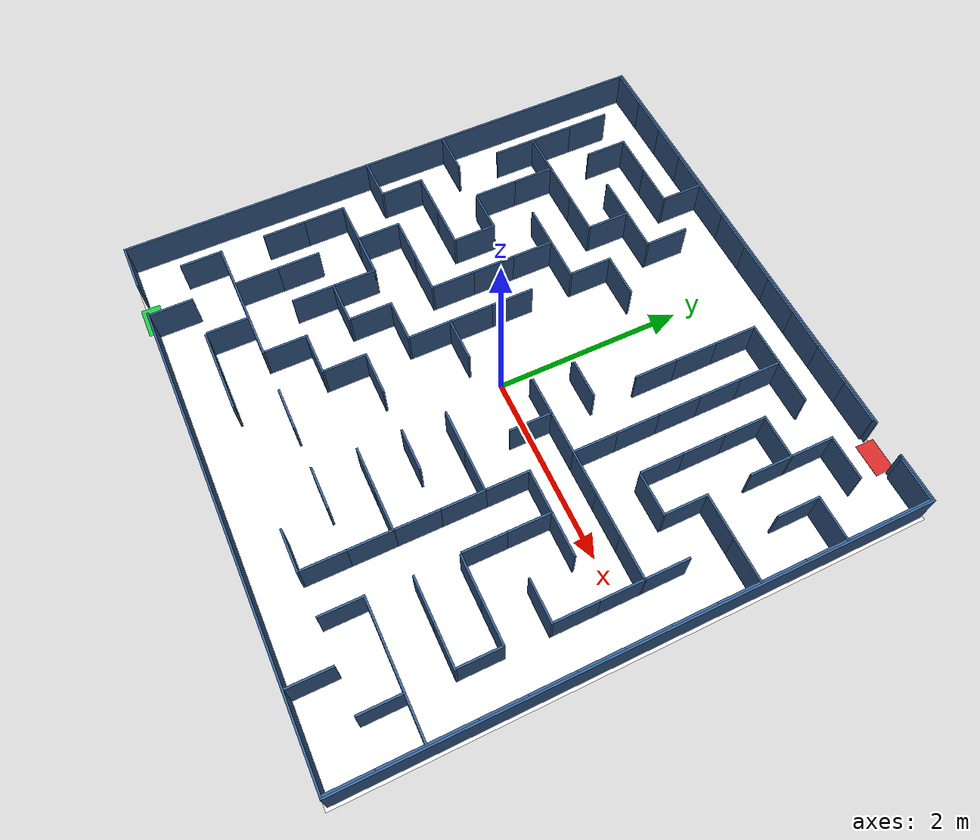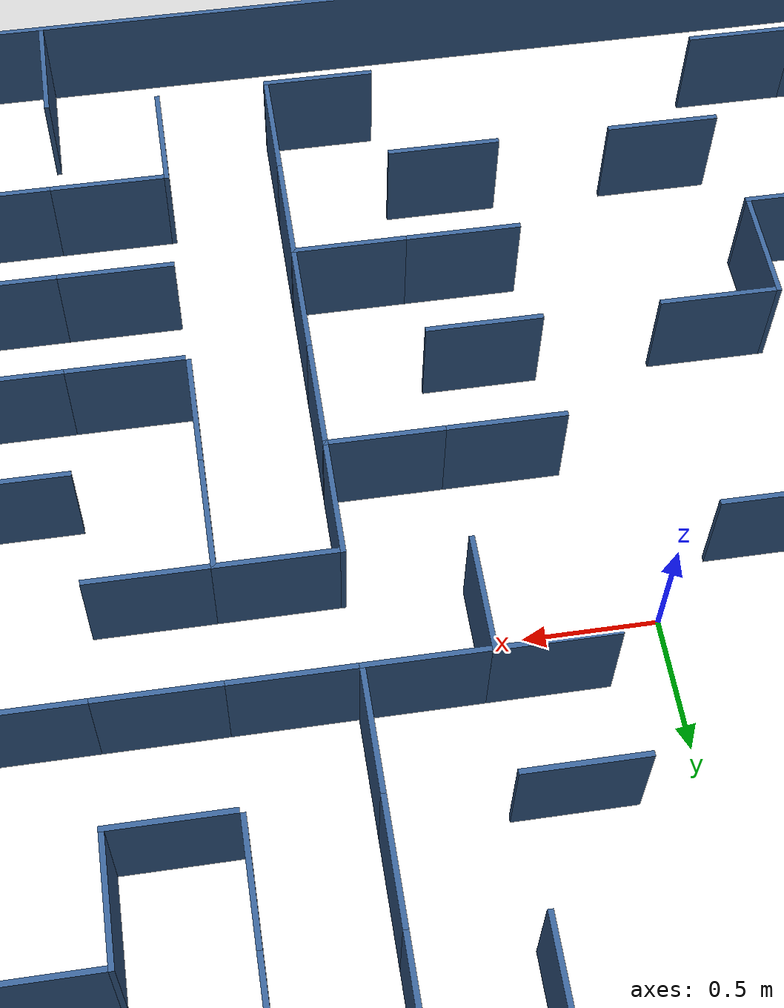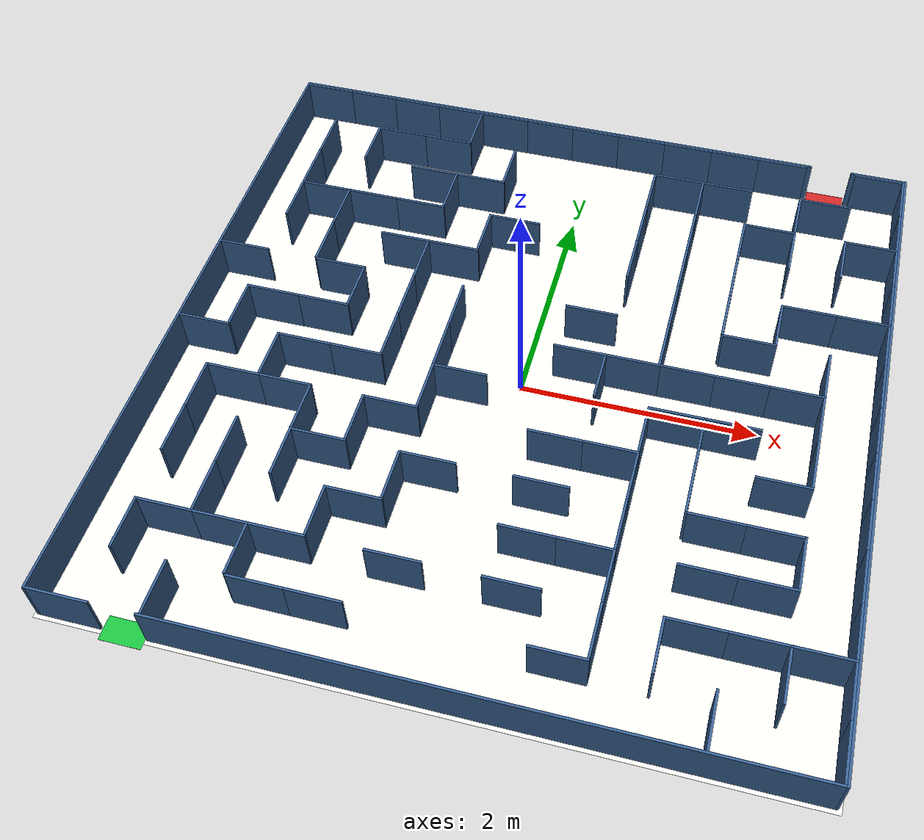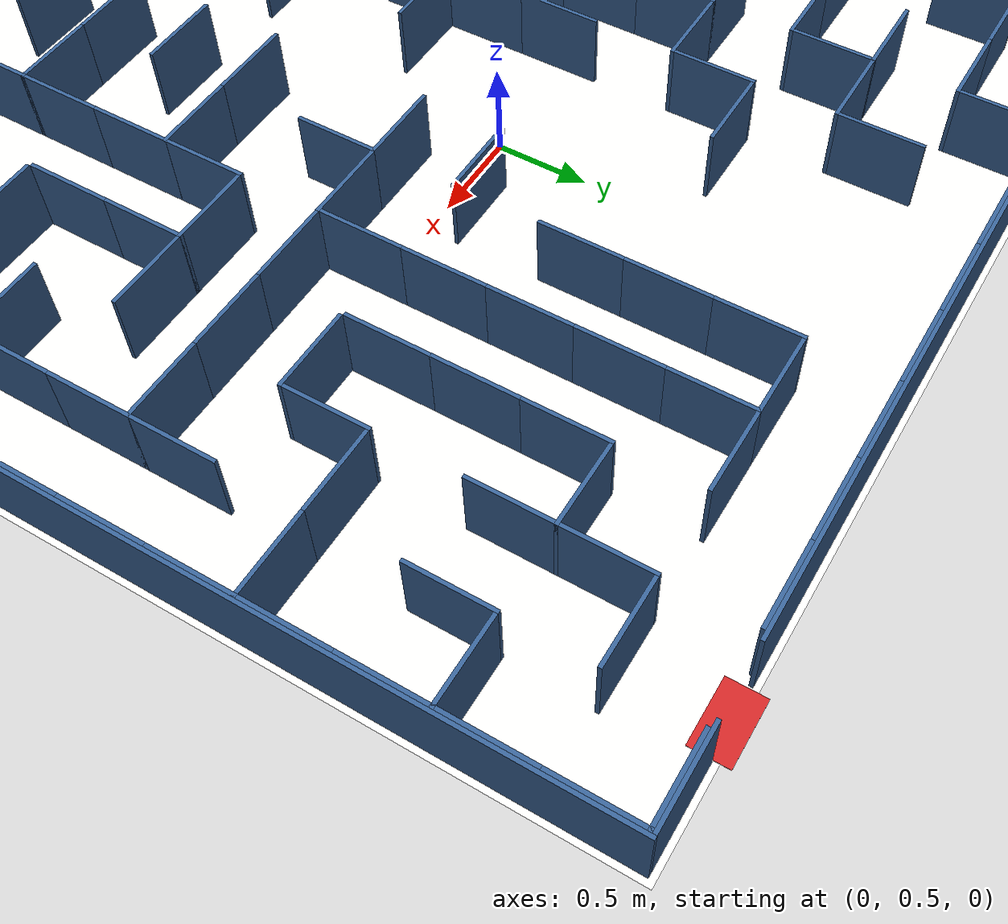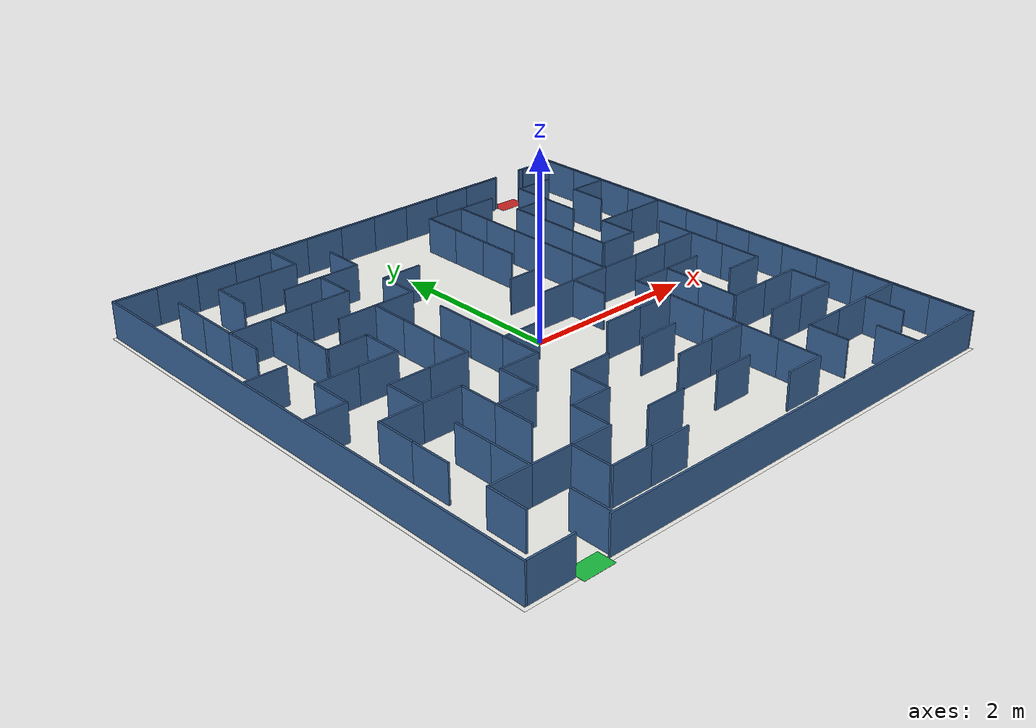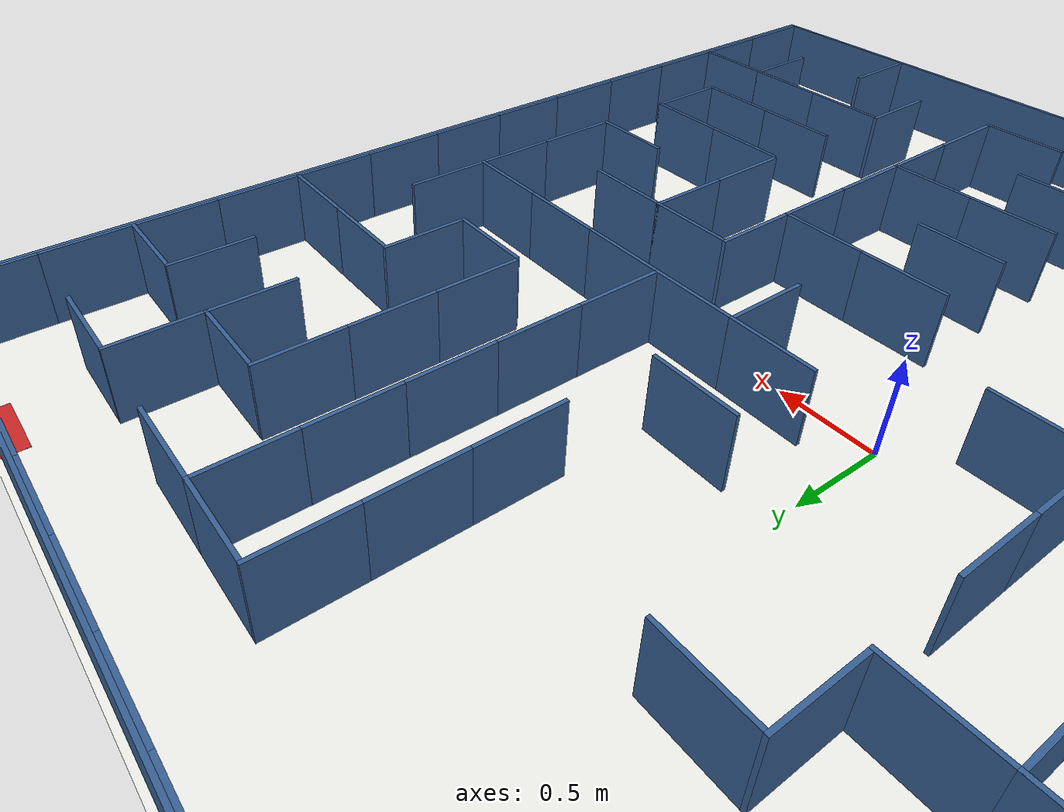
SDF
<?xml version="1.0" ?>
<sdf version="1.8">
  <world name="maze_world">

    <include>
      <uri>https://fuel.gazebosim.org/1.0/OpenRobotics/models/Sun</uri>
    </include>

    <plugin filename="gz-sim-physics-system"
            name="gz::sim::systems::Physics"/>

    <plugin filename="gz-sim-user-commands-system"
            name="gz::sim::systems::UserCommands"/>

    <plugin filename="gz-sim-scene-broadcaster-system"
            name="gz::sim::systems::SceneBroadcaster"/>

    <plugin filename="gz-sim-sensors-system"
            name="gz::sim::systems::Sensors">
      <render_engine>ogre2</render_engine>
    </plugin>

    <physics name="default_physics" type="dart">
      <max_step_size>0.001</max_step_size>
      <real_time_factor>1.0</real_time_factor>
      <real_time_update_rate>1000</real_time_update_rate>
    </physics>

    <scene>
      <ambient>0.4 0.4 0.4 1</ambient>
    </scene>

    <model name="white_floor">
      <static>true</static>
      <pose>0 0 0 0 0 0</pose>
      <link name="floor_link">
        <collision name="collision">
          <geometry>
            <plane>
              <normal>0 0 1</normal>
              <size>5.95 5.95</size>
            </plane>
          </geometry>
        </collision>
        <visual name="visual">
          <geometry>
            <plane>
              <normal>0 0 1</normal>
              <size>5.95 5.95</size>
            </plane>
          </geometry>
          <material>
            <ambient>0.92 0.92 0.9 1</ambient>
            <diffuse>0.95 0.95 0.93 1</diffuse>
            <specular>0.05 0.05 0.05 1</specular>
          </material>
        </visual>
      </link>
    </model>

    <model name="wall_outer_north_left">
      <static>true</static>
      <link name="link">
        <pose>-0.4275 2.935 0.2 0 0 0</pose>
        <collision name="collision">
          <geometry><box><size>4.995 0.04 0.4</size></box></geometry>
        </collision>
        <visual name="visual">
          <geometry><box><size>4.995 0.02 0.4</size></box></geometry>
          <material>
            <ambient>0.18 0.32 0.5 1</ambient>
            <diffuse>0.22 0.38 0.58 1</diffuse>
            <specular>0.15 0.15 0.15 1</specular>
          </material>
        </visual>
      </link>
    </model>

    <model name="wall_outer_north_right">
      <static>true</static>
      <link name="link">
        <pose>2.6775 2.935 0.2 0 0 0</pose>
        <collision name="collision">
          <geometry><box><size>0.495 0.04 0.4</size></box></geometry>
        </collision>
        <visual name="visual">
          <geometry><box><size>0.495 0.02 0.4</size></box></geometry>
          <material>
            <ambient>0.18 0.32 0.5 1</ambient>
            <diffuse>0.22 0.38 0.58 1</diffuse>
            <specular>0.15 0.15 0.15 1</specular>
          </material>
        </visual>
      </link>
    </model>

    <model name="wall_outer_south_left">
      <static>true</static>
      <link name="link">
        <pose>-2.6775 -2.935 0.2 0 0 0</pose>
        <collision name="collision">
          <geometry><box><size>0.495 0.04 0.4</size></box></geometry>
        </collision>
        <visual name="visual">
          <geometry><box><size>0.495 0.02 0.4</size></box></geometry>
          <material>
            <ambient>0.18 0.32 0.5 1</ambient>
            <diffuse>0.22 0.38 0.58 1</diffuse>
            <specular>0.15 0.15 0.15 1</specular>
          </material>
        </visual>
      </link>
    </model>

    <model name="wall_outer_south_right">
      <static>true</static>
      <link name="link">
        <pose>0.4275 -2.935 0.2 0 0 0</pose>
        <collision name="collision">
          <geometry><box><size>4.995 0.04 0.4</size></box></geometry>
        </collision>
        <visual name="visual">
          <geometry><box><size>4.995 0.02 0.4</size></box></geometry>
          <material>
            <ambient>0.18 0.32 0.5 1</ambient>
            <diffuse>0.22 0.38 0.58 1</diffuse>
            <specular>0.15 0.15 0.15 1</specular>
          </material>
        </visual>
      </link>
    </model>

    <model name="wall_outer_east">
      <static>true</static>
      <link name="link">
        <pose>2.935 0 0.2 0 0 0</pose>
        <collision name="collision">
          <geometry><box><size>0.04 5.890000000000001 0.4</size></box></geometry>
        </collision>
        <visual name="visual">
          <geometry><box><size>0.02 5.890000000000001 0.4</size></box></geometry>
          <material>
            <ambient>0.18 0.32 0.5 1</ambient>
            <diffuse>0.22 0.38 0.58 1</diffuse>
            <specular>0.15 0.15 0.15 1</specular>
          </material>
        </visual>
      </link>
    </model>

    <model name="wall_outer_west">
      <static>true</static>
      <link name="link">
        <pose>-2.935 0 0.2 0 0 0</pose>
        <collision name="collision">
          <geometry><box><size>0.04 5.890000000000001 0.4</size></box></geometry>
        </collision>
        <visual name="visual">
          <geometry><box><size>0.02 5.890000000000001 0.4</size></box></geometry>
          <material>
            <ambient>0.18 0.32 0.5 1</ambient>
            <diffuse>0.22 0.38 0.58 1</diffuse>
            <specular>0.15 0.15 0.15 1</specular>
          </material>
        </visual>
      </link>
    </model>

    <model name="wall_h_0_0">
      <static>true</static>
      <link name="link">
        <pose>-2.7 2.9150000000000005 0.2 0 0 0</pose>
        <collision name="collision"><geometry><box><size>0.45 0.04 0.4</size></box></geometry></collision>
        <visual name="visual">
          <geometry><box><size>0.45 0.02 0.4</size></box></geometry>
          <material>
            <ambient>0.18 0.32 0.5 1</ambient>
            <diffuse>0.22 0.38 0.58 1</diffuse>
            <specular>0.15 0.15 0.15 1</specular>
          </material>
        </visual>
      </link>
    </model>

    <model name="wall_h_0_1">
      <static>true</static>
      <link name="link">
        <pose>-2.25 2.9150000000000005 0.2 0 0 0</pose>
        <collision name="collision"><geometry><box><size>0.45 0.04 0.4</size></box></geometry></collision>
        <visual name="visual">
          <geometry><box><size>0.45 0.02 0.4</size></box></geometry>
          <material>
            <ambient>0.18 0.32 0.5 1</ambient>
            <diffuse>0.22 0.38 0.58 1</diffuse>
            <specular>0.15 0.15 0.15 1</specular>
          </material>
        </visual>
      </link>
    </model>

    <model name="wall_h_0_2">
      <static>true</static>
      <link name="link">
        <pose>-1.8000000000000003 2.9150000000000005 0.2 0 0 0</pose>
        <collision name="collision"><geometry><box><size>0.45 0.04 0.4</size></box></geometry></collision>
        <visual name="visual">
          <geometry><box><size>0.45 0.02 0.4</size></box></geometry>
          <material>
            <ambient>0.18 0.32 0.5 1</ambient>
            <diffuse>0.22 0.38 0.58 1</diffuse>
            <specular>0.15 0.15 0.15 1</specular>
          </material>
        </visual>
      </link>
    </model>

    <model name="wall_h_0_3">
      <static>true</static>
      <link name="link">
        <pose>-1.3500000000000003 2.9150000000000005 0.2 0 0 0</pose>
        <collision name="collision"><geometry><box><size>0.45 0.04 0.4</size></box></geometry></collision>
        <visual name="visual">
          <geometry><box><size>0.45 0.02 0.4</size></box></geometry>
          <material>
            <ambient>0.18 0.32 0.5 1</ambient>
            <diffuse>0.22 0.38 0.58 1</diffuse>
            <specular>0.15 0.15 0.15 1</specular>
          </material>
        </visual>
      </link>
    </model>

    <model name="wall_v_0_3">
      <static>true</static>
      <link name="link">
        <pose>-1.1350000000000002 2.7 0.2 0 0 0</pose>
        <collision name="collision"><geometry><box><size>0.04 0.45 0.4</size></box></geometry></collision>
        <visual name="visual">
          <geometry><box><size>0.02 0.45 0.4</size></box></geometry>
          <material>
            <ambient>0.18 0.32 0.5 1</ambient>
            <diffuse>0.22 0.38 0.58 1</diffuse>
            <specular>0.15 0.15 0.15 1</specular>
          </material>
        </visual>
      </link>
    </model>

    <model name="wall_h_0_4">
      <static>true</static>
      <link name="link">
        <pose>-0.9000000000000004 2.9150000000000005 0.2 0 0 0</pose>
        <collision name="collision"><geometry><box><size>0.45 0.04 0.4</size></box></geometry></collision>
        <visual name="visual">
          <geometry><box><size>0.45 0.02 0.4</size></box></geometry>
          <material>
            <ambient>0.18 0.32 0.5 1</ambient>
            <diffuse>0.22 0.38 0.58 1</diffuse>
            <specular>0.15 0.15 0.15 1</specular>
          </material>
        </visual>
      </link>
    </model>

    <model name="wall_h_0_5">
      <static>true</static>
      <link name="link">
        <pose>-0.4500000000000002 2.9150000000000005 0.2 0 0 0</pose>
        <collision name="collision"><geometry><box><size>0.45 0.04 0.4</size></box></geometry></collision>
        <visual name="visual">
          <geometry><box><size>0.45 0.02 0.4</size></box></geometry>
          <material>
            <ambient>0.18 0.32 0.5 1</ambient>
            <diffuse>0.22 0.38 0.58 1</diffuse>
            <specular>0.15 0.15 0.15 1</specular>
          </material>
        </visual>
      </link>
    </model>

    <model name="wall_h_0_6">
      <static>true</static>
      <link name="link">
        <pose>0.0 2.9150000000000005 0.2 0 0 0</pose>
        <collision name="collision"><geometry><box><size>0.45 0.04 0.4</size></box></geometry></collision>
        <visual name="visual">
          <geometry><box><size>0.45 0.02 0.4</size></box></geometry>
          <material>
            <ambient>0.18 0.32 0.5 1</ambient>
            <diffuse>0.22 0.38 0.58 1</diffuse>
            <specular>0.15 0.15 0.15 1</specular>
          </material>
        </visual>
      </link>
    </model>

    <model name="wall_h_0_7">
      <static>true</static>
      <link name="link">
        <pose>0.44999999999999973 2.9150000000000005 0.2 0 0 0</pose>
        <collision name="collision"><geometry><box><size>0.45 0.04 0.4</size></box></geometry></collision>
        <visual name="visual">
          <geometry><box><size>0.45 0.02 0.4</size></box></geometry>
          <material>
            <ambient>0.18 0.32 0.5 1</ambient>
            <diffuse>0.22 0.38 0.58 1</diffuse>
            <specular>0.15 0.15 0.15 1</specular>
          </material>
        </visual>
      </link>
    </model>

    <model name="wall_h_0_8">
      <static>true</static>
      <link name="link">
        <pose>0.8999999999999999 2.9150000000000005 0.2 0 0 0</pose>
        <collision name="collision"><geometry><box><size>0.45 0.04 0.4</size></box></geometry></collision>
        <visual name="visual">
          <geometry><box><size>0.45 0.02 0.4</size></box></geometry>
          <material>
            <ambient>0.18 0.32 0.5 1</ambient>
            <diffuse>0.22 0.38 0.58 1</diffuse>
            <specular>0.15 0.15 0.15 1</specular>
          </material>
        </visual>
      </link>
    </model>

    <model name="wall_h_0_9">
      <static>true</static>
      <link name="link">
        <pose>1.35 2.9150000000000005 0.2 0 0 0</pose>
        <collision name="collision"><geometry><box><size>0.45 0.04 0.4</size></box></geometry></collision>
        <visual name="visual">
          <geometry><box><size>0.45 0.02 0.4</size></box></geometry>
          <material>
            <ambient>0.18 0.32 0.5 1</ambient>
            <diffuse>0.22 0.38 0.58 1</diffuse>
            <specular>0.15 0.15 0.15 1</specular>
          </material>
        </visual>
      </link>
    </model>

    <model name="wall_h_0_10">
      <static>true</static>
      <link name="link">
        <pose>1.8000000000000003 2.9150000000000005 0.2 0 0 0</pose>
        <collision name="collision"><geometry><box><size>0.45 0.04 0.4</size></box></geometry></collision>
        <visual name="visual">
          <geometry><box><size>0.45 0.02 0.4</size></box></geometry>
          <material>
            <ambient>0.18 0.32 0.5 1</ambient>
            <diffuse>0.22 0.38 0.58 1</diffuse>
            <specular>0.15 0.15 0.15 1</specular>
          </material>
        </visual>
      </link>
    </model>

    <model name="wall_h_0_12">
      <static>true</static>
      <link name="link">
        <pose>2.6999999999999997 2.9150000000000005 0.2 0 0 0</pose>
        <collision name="collision"><geometry><box><size>0.45 0.04 0.4</size></box></geometry></collision>
        <visual name="visual">
          <geometry><box><size>0.45 0.02 0.4</size></box></geometry>
          <material>
            <ambient>0.18 0.32 0.5 1</ambient>
            <diffuse>0.22 0.38 0.58 1</diffuse>
            <specular>0.15 0.15 0.15 1</specular>
          </material>
        </visual>
      </link>
    </model>

    <model name="wall_v_0_12">
      <static>true</static>
      <link name="link">
        <pose>2.915 2.7 0.2 0 0 0</pose>
        <collision name="collision"><geometry><box><size>0.04 0.45 0.4</size></box></geometry></collision>
        <visual name="visual">
          <geometry><box><size>0.02 0.45 0.4</size></box></geometry>
          <material>
            <ambient>0.18 0.32 0.5 1</ambient>
            <diffuse>0.22 0.38 0.58 1</diffuse>
            <specular>0.15 0.15 0.15 1</specular>
          </material>
        </visual>
      </link>
    </model>

    <model name="wall_v_1_0">
      <static>true</static>
      <link name="link">
        <pose>-2.485 2.25 0.2 0 0 0</pose>
        <collision name="collision"><geometry><box><size>0.04 0.45 0.4</size></box></geometry></collision>
        <visual name="visual">
          <geometry><box><size>0.02 0.45 0.4</size></box></geometry>
          <material>
            <ambient>0.18 0.32 0.5 1</ambient>
            <diffuse>0.22 0.38 0.58 1</diffuse>
            <specular>0.15 0.15 0.15 1</specular>
          </material>
        </visual>
      </link>
    </model>

    <model name="wall_v_1_1">
      <static>true</static>
      <link name="link">
        <pose>-2.0349999999999997 2.25 0.2 0 0 0</pose>
        <collision name="collision"><geometry><box><size>0.04 0.45 0.4</size></box></geometry></collision>
        <visual name="visual">
          <geometry><box><size>0.02 0.45 0.4</size></box></geometry>
          <material>
            <ambient>0.18 0.32 0.5 1</ambient>
            <diffuse>0.22 0.38 0.58 1</diffuse>
            <specular>0.15 0.15 0.15 1</specular>
          </material>
        </visual>
      </link>
    </model>

    <model name="wall_h_1_2">
      <static>true</static>
      <link name="link">
        <pose>-1.8000000000000003 2.4650000000000003 0.2 0 0 0</pose>
        <collision name="collision"><geometry><box><size>0.45 0.04 0.4</size></box></geometry></collision>
        <visual name="visual">
          <geometry><box><size>0.45 0.02 0.4</size></box></geometry>
          <material>
            <ambient>0.18 0.32 0.5 1</ambient>
            <diffuse>0.22 0.38 0.58 1</diffuse>
            <specular>0.15 0.15 0.15 1</specular>
          </material>
        </visual>
      </link>
    </model>

    <model name="wall_h_1_3">
      <static>true</static>
      <link name="link">
        <pose>-1.3500000000000003 2.4650000000000003 0.2 0 0 0</pose>
        <collision name="collision"><geometry><box><size>0.45 0.04 0.4</size></box></geometry></collision>
        <visual name="visual">
          <geometry><box><size>0.45 0.02 0.4</size></box></geometry>
          <material>
            <ambient>0.18 0.32 0.5 1</ambient>
            <diffuse>0.22 0.38 0.58 1</diffuse>
            <specular>0.15 0.15 0.15 1</specular>
          </material>
        </visual>
      </link>
    </model>

    <model name="wall_v_1_4">
      <static>true</static>
      <link name="link">
        <pose>-0.6850000000000004 2.25 0.2 0 0 0</pose>
        <collision name="collision"><geometry><box><size>0.04 0.45 0.4</size></box></geometry></collision>
        <visual name="visual">
          <geometry><box><size>0.02 0.45 0.4</size></box></geometry>
          <material>
            <ambient>0.18 0.32 0.5 1</ambient>
            <diffuse>0.22 0.38 0.58 1</diffuse>
            <specular>0.15 0.15 0.15 1</specular>
          </material>
        </visual>
      </link>
    </model>

    <model name="wall_v_1_7">
      <static>true</static>
      <link name="link">
        <pose>0.6649999999999997 2.25 0.2 0 0 0</pose>
        <collision name="collision"><geometry><box><size>0.04 0.45 0.4</size></box></geometry></collision>
        <visual name="visual">
          <geometry><box><size>0.02 0.45 0.4</size></box></geometry>
          <material>
            <ambient>0.18 0.32 0.5 1</ambient>
            <diffuse>0.22 0.38 0.58 1</diffuse>
            <specular>0.15 0.15 0.15 1</specular>
          </material>
        </visual>
      </link>
    </model>

    <model name="wall_h_1_8">
      <static>true</static>
      <link name="link">
        <pose>0.8999999999999999 2.4650000000000003 0.2 0 0 0</pose>
        <collision name="collision"><geometry><box><size>0.45 0.04 0.4</size></box></geometry></collision>
        <visual name="visual">
          <geometry><box><size>0.45 0.02 0.4</size></box></geometry>
          <material>
            <ambient>0.18 0.32 0.5 1</ambient>
            <diffuse>0.22 0.38 0.58 1</diffuse>
            <specular>0.15 0.15 0.15 1</specular>
          </material>
        </visual>
      </link>
    </model>

    <model name="wall_v_1_8">
      <static>true</static>
      <link name="link">
        <pose>1.115 2.25 0.2 0 0 0</pose>
        <collision name="collision"><geometry><box><size>0.04 0.45 0.4</size></box></geometry></collision>
        <visual name="visual">
          <geometry><box><size>0.02 0.45 0.4</size></box></geometry>
          <material>
            <ambient>0.18 0.32 0.5 1</ambient>
            <diffuse>0.22 0.38 0.58 1</diffuse>
            <specular>0.15 0.15 0.15 1</specular>
          </material>
        </visual>
      </link>
    </model>

    <model name="wall_h_1_9">
      <static>true</static>
      <link name="link">
        <pose>1.35 2.4650000000000003 0.2 0 0 0</pose>
        <collision name="collision"><geometry><box><size>0.45 0.04 0.4</size></box></geometry></collision>
        <visual name="visual">
          <geometry><box><size>0.45 0.02 0.4</size></box></geometry>
          <material>
            <ambient>0.18 0.32 0.5 1</ambient>
            <diffuse>0.22 0.38 0.58 1</diffuse>
            <specular>0.15 0.15 0.15 1</specular>
          </material>
        </visual>
      </link>
    </model>

    <model name="wall_v_1_10">
      <static>true</static>
      <link name="link">
        <pose>2.0150000000000006 2.25 0.2 0 0 0</pose>
        <collision name="collision"><geometry><box><size>0.04 0.45 0.4</size></box></geometry></collision>
        <visual name="visual">
          <geometry><box><size>0.02 0.45 0.4</size></box></geometry>
          <material>
            <ambient>0.18 0.32 0.5 1</ambient>
            <diffuse>0.22 0.38 0.58 1</diffuse>
            <specular>0.15 0.15 0.15 1</specular>
          </material>
        </visual>
      </link>
    </model>

    <model name="wall_h_1_11">
      <static>true</static>
      <link name="link">
        <pose>2.2499999999999996 2.4650000000000003 0.2 0 0 0</pose>
        <collision name="collision"><geometry><box><size>0.45 0.04 0.4</size></box></geometry></collision>
        <visual name="visual">
          <geometry><box><size>0.45 0.02 0.4</size></box></geometry>
          <material>
            <ambient>0.18 0.32 0.5 1</ambient>
            <diffuse>0.22 0.38 0.58 1</diffuse>
            <specular>0.15 0.15 0.15 1</specular>
          </material>
        </visual>
      </link>
    </model>

    <model name="wall_v_1_12">
      <static>true</static>
      <link name="link">
        <pose>2.915 2.25 0.2 0 0 0</pose>
        <collision name="collision"><geometry><box><size>0.04 0.45 0.4</size></box></geometry></collision>
        <visual name="visual">
          <geometry><box><size>0.02 0.45 0.4</size></box></geometry>
          <material>
            <ambient>0.18 0.32 0.5 1</ambient>
            <diffuse>0.22 0.38 0.58 1</diffuse>
            <specular>0.15 0.15 0.15 1</specular>
          </material>
        </visual>
      </link>
    </model>

    <model name="wall_v_2_0">
      <static>true</static>
      <link name="link">
        <pose>-2.485 1.8000000000000003 0.2 0 0 0</pose>
        <collision name="collision"><geometry><box><size>0.04 0.45 0.4</size></box></geometry></collision>
        <visual name="visual">
          <geometry><box><size>0.02 0.45 0.4</size></box></geometry>
          <material>
            <ambient>0.18 0.32 0.5 1</ambient>
            <diffuse>0.22 0.38 0.58 1</diffuse>
            <specular>0.15 0.15 0.15 1</specular>
          </material>
        </visual>
      </link>
    </model>

    <model name="wall_h_2_3">
      <static>true</static>
      <link name="link">
        <pose>-1.3500000000000003 2.0150000000000006 0.2 0 0 0</pose>
        <collision name="collision"><geometry><box><size>0.45 0.04 0.4</size></box></geometry></collision>
        <visual name="visual">
          <geometry><box><size>0.45 0.02 0.4</size></box></geometry>
          <material>
            <ambient>0.18 0.32 0.5 1</ambient>
            <diffuse>0.22 0.38 0.58 1</diffuse>
            <specular>0.15 0.15 0.15 1</specular>
          </material>
        </visual>
      </link>
    </model>

    <model name="wall_v_2_3">
      <static>true</static>
      <link name="link">
        <pose>-1.1350000000000002 1.8000000000000003 0.2 0 0 0</pose>
        <collision name="collision"><geometry><box><size>0.04 0.45 0.4</size></box></geometry></collision>
        <visual name="visual">
          <geometry><box><size>0.02 0.45 0.4</size></box></geometry>
          <material>
            <ambient>0.18 0.32 0.5 1</ambient>
            <diffuse>0.22 0.38 0.58 1</diffuse>
            <specular>0.15 0.15 0.15 1</specular>
          </material>
        </visual>
      </link>
    </model>

    <model name="wall_h_2_4">
      <static>true</static>
      <link name="link">
        <pose>-0.9000000000000004 2.0150000000000006 0.2 0 0 0</pose>
        <collision name="collision"><geometry><box><size>0.45 0.04 0.4</size></box></geometry></collision>
        <visual name="visual">
          <geometry><box><size>0.45 0.02 0.4</size></box></geometry>
          <material>
            <ambient>0.18 0.32 0.5 1</ambient>
            <diffuse>0.22 0.38 0.58 1</diffuse>
            <specular>0.15 0.15 0.15 1</specular>
          </material>
        </visual>
      </link>
    </model>

    <model name="wall_v_2_7">
      <static>true</static>
      <link name="link">
        <pose>0.6649999999999997 1.8000000000000003 0.2 0 0 0</pose>
        <collision name="collision"><geometry><box><size>0.04 0.45 0.4</size></box></geometry></collision>
        <visual name="visual">
          <geometry><box><size>0.02 0.45 0.4</size></box></geometry>
          <material>
            <ambient>0.18 0.32 0.5 1</ambient>
            <diffuse>0.22 0.38 0.58 1</diffuse>
            <specular>0.15 0.15 0.15 1</specular>
          </material>
        </visual>
      </link>
    </model>

    <model name="wall_v_2_8">
      <static>true</static>
      <link name="link">
        <pose>1.115 1.8000000000000003 0.2 0 0 0</pose>
        <collision name="collision"><geometry><box><size>0.04 0.45 0.4</size></box></geometry></collision>
        <visual name="visual">
          <geometry><box><size>0.02 0.45 0.4</size></box></geometry>
          <material>
            <ambient>0.18 0.32 0.5 1</ambient>
            <diffuse>0.22 0.38 0.58 1</diffuse>
            <specular>0.15 0.15 0.15 1</specular>
          </material>
        </visual>
      </link>
    </model>

    <model name="wall_v_2_9">
      <static>true</static>
      <link name="link">
        <pose>1.5650000000000002 1.8000000000000003 0.2 0 0 0</pose>
        <collision name="collision"><geometry><box><size>0.04 0.45 0.4</size></box></geometry></collision>
        <visual name="visual">
          <geometry><box><size>0.02 0.45 0.4</size></box></geometry>
          <material>
            <ambient>0.18 0.32 0.5 1</ambient>
            <diffuse>0.22 0.38 0.58 1</diffuse>
            <specular>0.15 0.15 0.15 1</specular>
          </material>
        </visual>
      </link>
    </model>

    <model name="wall_h_2_10">
      <static>true</static>
      <link name="link">
        <pose>1.8000000000000003 2.0150000000000006 0.2 0 0 0</pose>
        <collision name="collision"><geometry><box><size>0.45 0.04 0.4</size></box></geometry></collision>
        <visual name="visual">
          <geometry><box><size>0.45 0.02 0.4</size></box></geometry>
          <material>
            <ambient>0.18 0.32 0.5 1</ambient>
            <diffuse>0.22 0.38 0.58 1</diffuse>
            <specular>0.15 0.15 0.15 1</specular>
          </material>
        </visual>
      </link>
    </model>

    <model name="wall_v_2_10">
      <static>true</static>
      <link name="link">
        <pose>2.0150000000000006 1.8000000000000003 0.2 0 0 0</pose>
        <collision name="collision"><geometry><box><size>0.04 0.45 0.4</size></box></geometry></collision>
        <visual name="visual">
          <geometry><box><size>0.02 0.45 0.4</size></box></geometry>
          <material>
            <ambient>0.18 0.32 0.5 1</ambient>
            <diffuse>0.22 0.38 0.58 1</diffuse>
            <specular>0.15 0.15 0.15 1</specular>
          </material>
        </visual>
      </link>
    </model>

    <model name="wall_v_2_11">
      <static>true</static>
      <link name="link">
        <pose>2.465 1.8000000000000003 0.2 0 0 0</pose>
        <collision name="collision"><geometry><box><size>0.04 0.45 0.4</size></box></geometry></collision>
        <visual name="visual">
          <geometry><box><size>0.02 0.45 0.4</size></box></geometry>
          <material>
            <ambient>0.18 0.32 0.5 1</ambient>
            <diffuse>0.22 0.38 0.58 1</diffuse>
            <specular>0.15 0.15 0.15 1</specular>
          </material>
        </visual>
      </link>
    </model>

    <model name="wall_h_2_12">
      <static>true</static>
      <link name="link">
        <pose>2.6999999999999997 2.0150000000000006 0.2 0 0 0</pose>
        <collision name="collision"><geometry><box><size>0.45 0.04 0.4</size></box></geometry></collision>
        <visual name="visual">
          <geometry><box><size>0.45 0.02 0.4</size></box></geometry>
          <material>
            <ambient>0.18 0.32 0.5 1</ambient>
            <diffuse>0.22 0.38 0.58 1</diffuse>
            <specular>0.15 0.15 0.15 1</specular>
          </material>
        </visual>
      </link>
    </model>

    <model name="wall_v_2_12">
      <static>true</static>
      <link name="link">
        <pose>2.915 1.8000000000000003 0.2 0 0 0</pose>
        <collision name="collision"><geometry><box><size>0.04 0.45 0.4</size></box></geometry></collision>
        <visual name="visual">
          <geometry><box><size>0.02 0.45 0.4</size></box></geometry>
          <material>
            <ambient>0.18 0.32 0.5 1</ambient>
            <diffuse>0.22 0.38 0.58 1</diffuse>
            <specular>0.15 0.15 0.15 1</specular>
          </material>
        </visual>
      </link>
    </model>

    <model name="wall_v_3_0">
      <static>true</static>
      <link name="link">
        <pose>-2.485 1.3500000000000003 0.2 0 0 0</pose>
        <collision name="collision"><geometry><box><size>0.04 0.45 0.4</size></box></geometry></collision>
        <visual name="visual">
          <geometry><box><size>0.02 0.45 0.4</size></box></geometry>
          <material>
            <ambient>0.18 0.32 0.5 1</ambient>
            <diffuse>0.22 0.38 0.58 1</diffuse>
            <specular>0.15 0.15 0.15 1</specular>
          </material>
        </visual>
      </link>
    </model>

    <model name="wall_h_3_1">
      <static>true</static>
      <link name="link">
        <pose>-2.25 1.5650000000000004 0.2 0 0 0</pose>
        <collision name="collision"><geometry><box><size>0.45 0.04 0.4</size></box></geometry></collision>
        <visual name="visual">
          <geometry><box><size>0.45 0.02 0.4</size></box></geometry>
          <material>
            <ambient>0.18 0.32 0.5 1</ambient>
            <diffuse>0.22 0.38 0.58 1</diffuse>
            <specular>0.15 0.15 0.15 1</specular>
          </material>
        </visual>
      </link>
    </model>

    <model name="wall_v_3_1">
      <static>true</static>
      <link name="link">
        <pose>-2.0349999999999997 1.3500000000000003 0.2 0 0 0</pose>
        <collision name="collision"><geometry><box><size>0.04 0.45 0.4</size></box></geometry></collision>
        <visual name="visual">
          <geometry><box><size>0.02 0.45 0.4</size></box></geometry>
          <material>
            <ambient>0.18 0.32 0.5 1</ambient>
            <diffuse>0.22 0.38 0.58 1</diffuse>
            <specular>0.15 0.15 0.15 1</specular>
          </material>
        </visual>
      </link>
    </model>

    <model name="wall_h_3_2">
      <static>true</static>
      <link name="link">
        <pose>-1.8000000000000003 1.5650000000000004 0.2 0 0 0</pose>
        <collision name="collision"><geometry><box><size>0.45 0.04 0.4</size></box></geometry></collision>
        <visual name="visual">
          <geometry><box><size>0.45 0.02 0.4</size></box></geometry>
          <material>
            <ambient>0.18 0.32 0.5 1</ambient>
            <diffuse>0.22 0.38 0.58 1</diffuse>
            <specular>0.15 0.15 0.15 1</specular>
          </material>
        </visual>
      </link>
    </model>

    <model name="wall_h_3_3">
      <static>true</static>
      <link name="link">
        <pose>-1.3500000000000003 1.5650000000000004 0.2 0 0 0</pose>
        <collision name="collision"><geometry><box><size>0.45 0.04 0.4</size></box></geometry></collision>
        <visual name="visual">
          <geometry><box><size>0.45 0.02 0.4</size></box></geometry>
          <material>
            <ambient>0.18 0.32 0.5 1</ambient>
            <diffuse>0.22 0.38 0.58 1</diffuse>
            <specular>0.15 0.15 0.15 1</specular>
          </material>
        </visual>
      </link>
    </model>

    <model name="wall_v_3_4">
      <static>true</static>
      <link name="link">
        <pose>-0.6850000000000004 1.3500000000000003 0.2 0 0 0</pose>
        <collision name="collision"><geometry><box><size>0.04 0.45 0.4</size></box></geometry></collision>
        <visual name="visual">
          <geometry><box><size>0.02 0.45 0.4</size></box></geometry>
          <material>
            <ambient>0.18 0.32 0.5 1</ambient>
            <diffuse>0.22 0.38 0.58 1</diffuse>
            <specular>0.15 0.15 0.15 1</specular>
          </material>
        </visual>
      </link>
    </model>

    <model name="wall_h_3_5">
      <static>true</static>
      <link name="link">
        <pose>-0.4500000000000002 1.5650000000000004 0.2 0 0 0</pose>
        <collision name="collision"><geometry><box><size>0.45 0.04 0.4</size></box></geometry></collision>
        <visual name="visual">
          <geometry><box><size>0.45 0.02 0.4</size></box></geometry>
          <material>
            <ambient>0.18 0.32 0.5 1</ambient>
            <diffuse>0.22 0.38 0.58 1</diffuse>
            <specular>0.15 0.15 0.15 1</specular>
          </material>
        </visual>
      </link>
    </model>

    <model name="wall_v_3_7">
      <static>true</static>
      <link name="link">
        <pose>0.6649999999999997 1.3500000000000003 0.2 0 0 0</pose>
        <collision name="collision"><geometry><box><size>0.04 0.45 0.4</size></box></geometry></collision>
        <visual name="visual">
          <geometry><box><size>0.02 0.45 0.4</size></box></geometry>
          <material>
            <ambient>0.18 0.32 0.5 1</ambient>
            <diffuse>0.22 0.38 0.58 1</diffuse>
            <specular>0.15 0.15 0.15 1</specular>
          </material>
        </visual>
      </link>
    </model>

    <model name="wall_v_3_8">
      <static>true</static>
      <link name="link">
        <pose>1.115 1.3500000000000003 0.2 0 0 0</pose>
        <collision name="collision"><geometry><box><size>0.04 0.45 0.4</size></box></geometry></collision>
        <visual name="visual">
          <geometry><box><size>0.02 0.45 0.4</size></box></geometry>
          <material>
            <ambient>0.18 0.32 0.5 1</ambient>
            <diffuse>0.22 0.38 0.58 1</diffuse>
            <specular>0.15 0.15 0.15 1</specular>
          </material>
        </visual>
      </link>
    </model>

    <model name="wall_v_3_9">
      <static>true</static>
      <link name="link">
        <pose>1.5650000000000002 1.3500000000000003 0.2 0 0 0</pose>
        <collision name="collision"><geometry><box><size>0.04 0.45 0.4</size></box></geometry></collision>
        <visual name="visual">
          <geometry><box><size>0.02 0.45 0.4</size></box></geometry>
          <material>
            <ambient>0.18 0.32 0.5 1</ambient>
            <diffuse>0.22 0.38 0.58 1</diffuse>
            <specular>0.15 0.15 0.15 1</specular>
          </material>
        </visual>
      </link>
    </model>

    <model name="wall_v_3_12">
      <static>true</static>
      <link name="link">
        <pose>2.915 1.3500000000000003 0.2 0 0 0</pose>
        <collision name="collision"><geometry><box><size>0.04 0.45 0.4</size></box></geometry></collision>
        <visual name="visual">
          <geometry><box><size>0.02 0.45 0.4</size></box></geometry>
          <material>
            <ambient>0.18 0.32 0.5 1</ambient>
            <diffuse>0.22 0.38 0.58 1</diffuse>
            <specular>0.15 0.15 0.15 1</specular>
          </material>
        </visual>
      </link>
    </model>

    <model name="wall_v_4_1">
      <static>true</static>
      <link name="link">
        <pose>-2.0349999999999997 0.9000000000000004 0.2 0 0 0</pose>
        <collision name="collision"><geometry><box><size>0.04 0.45 0.4</size></box></geometry></collision>
        <visual name="visual">
          <geometry><box><size>0.02 0.45 0.4</size></box></geometry>
          <material>
            <ambient>0.18 0.32 0.5 1</ambient>
            <diffuse>0.22 0.38 0.58 1</diffuse>
            <specular>0.15 0.15 0.15 1</specular>
          </material>
        </visual>
      </link>
    </model>

    <model name="wall_h_4_3">
      <static>true</static>
      <link name="link">
        <pose>-1.3500000000000003 1.1150000000000004 0.2 0 0 0</pose>
        <collision name="collision"><geometry><box><size>0.45 0.04 0.4</size></box></geometry></collision>
        <visual name="visual">
          <geometry><box><size>0.45 0.02 0.4</size></box></geometry>
          <material>
            <ambient>0.18 0.32 0.5 1</ambient>
            <diffuse>0.22 0.38 0.58 1</diffuse>
            <specular>0.15 0.15 0.15 1</specular>
          </material>
        </visual>
      </link>
    </model>

    <model name="wall_v_4_3">
      <static>true</static>
      <link name="link">
        <pose>-1.1350000000000002 0.9000000000000004 0.2 0 0 0</pose>
        <collision name="collision"><geometry><box><size>0.04 0.45 0.4</size></box></geometry></collision>
        <visual name="visual">
          <geometry><box><size>0.02 0.45 0.4</size></box></geometry>
          <material>
            <ambient>0.18 0.32 0.5 1</ambient>
            <diffuse>0.22 0.38 0.58 1</diffuse>
            <specular>0.15 0.15 0.15 1</specular>
          </material>
        </visual>
      </link>
    </model>

    <model name="wall_h_4_4">
      <static>true</static>
      <link name="link">
        <pose>-0.9000000000000004 1.1150000000000004 0.2 0 0 0</pose>
        <collision name="collision"><geometry><box><size>0.45 0.04 0.4</size></box></geometry></collision>
        <visual name="visual">
          <geometry><box><size>0.45 0.02 0.4</size></box></geometry>
          <material>
            <ambient>0.18 0.32 0.5 1</ambient>
            <diffuse>0.22 0.38 0.58 1</diffuse>
            <specular>0.15 0.15 0.15 1</specular>
          </material>
        </visual>
      </link>
    </model>

    <model name="wall_v_4_8">
      <static>true</static>
      <link name="link">
        <pose>1.115 0.9000000000000004 0.2 0 0 0</pose>
        <collision name="collision"><geometry><box><size>0.04 0.45 0.4</size></box></geometry></collision>
        <visual name="visual">
          <geometry><box><size>0.02 0.45 0.4</size></box></geometry>
          <material>
            <ambient>0.18 0.32 0.5 1</ambient>
            <diffuse>0.22 0.38 0.58 1</diffuse>
            <specular>0.15 0.15 0.15 1</specular>
          </material>
        </visual>
      </link>
    </model>

    <model name="wall_v_4_9">
      <static>true</static>
      <link name="link">
        <pose>1.5650000000000002 0.9000000000000004 0.2 0 0 0</pose>
        <collision name="collision"><geometry><box><size>0.04 0.45 0.4</size></box></geometry></collision>
        <visual name="visual">
          <geometry><box><size>0.02 0.45 0.4</size></box></geometry>
          <material>
            <ambient>0.18 0.32 0.5 1</ambient>
            <diffuse>0.22 0.38 0.58 1</diffuse>
            <specular>0.15 0.15 0.15 1</specular>
          </material>
        </visual>
      </link>
    </model>

    <model name="wall_v_4_10">
      <static>true</static>
      <link name="link">
        <pose>2.0150000000000006 0.9000000000000004 0.2 0 0 0</pose>
        <collision name="collision"><geometry><box><size>0.04 0.45 0.4</size></box></geometry></collision>
        <visual name="visual">
          <geometry><box><size>0.02 0.45 0.4</size></box></geometry>
          <material>
            <ambient>0.18 0.32 0.5 1</ambient>
            <diffuse>0.22 0.38 0.58 1</diffuse>
            <specular>0.15 0.15 0.15 1</specular>
          </material>
        </visual>
      </link>
    </model>

    <model name="wall_h_4_11">
      <static>true</static>
      <link name="link">
        <pose>2.2499999999999996 1.1150000000000004 0.2 0 0 0</pose>
        <collision name="collision"><geometry><box><size>0.45 0.04 0.4</size></box></geometry></collision>
        <visual name="visual">
          <geometry><box><size>0.45 0.02 0.4</size></box></geometry>
          <material>
            <ambient>0.18 0.32 0.5 1</ambient>
            <diffuse>0.22 0.38 0.58 1</diffuse>
            <specular>0.15 0.15 0.15 1</specular>
          </material>
        </visual>
      </link>
    </model>

    <model name="wall_h_4_12">
      <static>true</static>
      <link name="link">
        <pose>2.6999999999999997 1.1150000000000004 0.2 0 0 0</pose>
        <collision name="collision"><geometry><box><size>0.45 0.04 0.4</size></box></geometry></collision>
        <visual name="visual">
          <geometry><box><size>0.45 0.02 0.4</size></box></geometry>
          <material>
            <ambient>0.18 0.32 0.5 1</ambient>
            <diffuse>0.22 0.38 0.58 1</diffuse>
            <specular>0.15 0.15 0.15 1</specular>
          </material>
        </visual>
      </link>
    </model>

    <model name="wall_v_4_12">
      <static>true</static>
      <link name="link">
        <pose>2.915 0.9000000000000004 0.2 0 0 0</pose>
        <collision name="collision"><geometry><box><size>0.04 0.45 0.4</size></box></geometry></collision>
        <visual name="visual">
          <geometry><box><size>0.02 0.45 0.4</size></box></geometry>
          <material>
            <ambient>0.18 0.32 0.5 1</ambient>
            <diffuse>0.22 0.38 0.58 1</diffuse>
            <specular>0.15 0.15 0.15 1</specular>
          </material>
        </visual>
      </link>
    </model>

    <model name="wall_h_5_0">
      <static>true</static>
      <link name="link">
        <pose>-2.7 0.6650000000000001 0.2 0 0 0</pose>
        <collision name="collision"><geometry><box><size>0.45 0.04 0.4</size></box></geometry></collision>
        <visual name="visual">
          <geometry><box><size>0.45 0.02 0.4</size></box></geometry>
          <material>
            <ambient>0.18 0.32 0.5 1</ambient>
            <diffuse>0.22 0.38 0.58 1</diffuse>
            <specular>0.15 0.15 0.15 1</specular>
          </material>
        </visual>
      </link>
    </model>

    <model name="wall_h_5_2">
      <static>true</static>
      <link name="link">
        <pose>-1.8000000000000003 0.6650000000000001 0.2 0 0 0</pose>
        <collision name="collision"><geometry><box><size>0.45 0.04 0.4</size></box></geometry></collision>
        <visual name="visual">
          <geometry><box><size>0.45 0.02 0.4</size></box></geometry>
          <material>
            <ambient>0.18 0.32 0.5 1</ambient>
            <diffuse>0.22 0.38 0.58 1</diffuse>
            <specular>0.15 0.15 0.15 1</specular>
          </material>
        </visual>
      </link>
    </model>

    <model name="wall_v_5_2">
      <static>true</static>
      <link name="link">
        <pose>-1.5850000000000002 0.4500000000000002 0.2 0 0 0</pose>
        <collision name="collision"><geometry><box><size>0.04 0.45 0.4</size></box></geometry></collision>
        <visual name="visual">
          <geometry><box><size>0.02 0.45 0.4</size></box></geometry>
          <material>
            <ambient>0.18 0.32 0.5 1</ambient>
            <diffuse>0.22 0.38 0.58 1</diffuse>
            <specular>0.15 0.15 0.15 1</specular>
          </material>
        </visual>
      </link>
    </model>

    <model name="wall_v_5_3">
      <static>true</static>
      <link name="link">
        <pose>-1.1350000000000002 0.4500000000000002 0.2 0 0 0</pose>
        <collision name="collision"><geometry><box><size>0.04 0.45 0.4</size></box></geometry></collision>
        <visual name="visual">
          <geometry><box><size>0.02 0.45 0.4</size></box></geometry>
          <material>
            <ambient>0.18 0.32 0.5 1</ambient>
            <diffuse>0.22 0.38 0.58 1</diffuse>
            <specular>0.15 0.15 0.15 1</specular>
          </material>
        </visual>
      </link>
    </model>

    <model name="wall_v_5_4">
      <static>true</static>
      <link name="link">
        <pose>-0.6850000000000004 0.4500000000000002 0.2 0 0 0</pose>
        <collision name="collision"><geometry><box><size>0.04 0.45 0.4</size></box></geometry></collision>
        <visual name="visual">
          <geometry><box><size>0.02 0.45 0.4</size></box></geometry>
          <material>
            <ambient>0.18 0.32 0.5 1</ambient>
            <diffuse>0.22 0.38 0.58 1</diffuse>
            <specular>0.15 0.15 0.15 1</specular>
          </material>
        </visual>
      </link>
    </model>

    <model name="wall_h_5_7">
      <static>true</static>
      <link name="link">
        <pose>0.44999999999999973 0.6650000000000001 0.2 0 0 0</pose>
        <collision name="collision"><geometry><box><size>0.45 0.04 0.4</size></box></geometry></collision>
        <visual name="visual">
          <geometry><box><size>0.45 0.02 0.4</size></box></geometry>
          <material>
            <ambient>0.18 0.32 0.5 1</ambient>
            <diffuse>0.22 0.38 0.58 1</diffuse>
            <specular>0.15 0.15 0.15 1</specular>
          </material>
        </visual>
      </link>
    </model>

    <model name="wall_v_5_8">
      <static>true</static>
      <link name="link">
        <pose>1.115 0.4500000000000002 0.2 0 0 0</pose>
        <collision name="collision"><geometry><box><size>0.04 0.45 0.4</size></box></geometry></collision>
        <visual name="visual">
          <geometry><box><size>0.02 0.45 0.4</size></box></geometry>
          <material>
            <ambient>0.18 0.32 0.5 1</ambient>
            <diffuse>0.22 0.38 0.58 1</diffuse>
            <specular>0.15 0.15 0.15 1</specular>
          </material>
        </visual>
      </link>
    </model>

    <model name="wall_h_5_10">
      <static>true</static>
      <link name="link">
        <pose>1.8000000000000003 0.6650000000000001 0.2 0 0 0</pose>
        <collision name="collision"><geometry><box><size>0.45 0.04 0.4</size></box></geometry></collision>
        <visual name="visual">
          <geometry><box><size>0.45 0.02 0.4</size></box></geometry>
          <material>
            <ambient>0.18 0.32 0.5 1</ambient>
            <diffuse>0.22 0.38 0.58 1</diffuse>
            <specular>0.15 0.15 0.15 1</specular>
          </material>
        </visual>
      </link>
    </model>

    <model name="wall_v_5_11">
      <static>true</static>
      <link name="link">
        <pose>2.465 0.4500000000000002 0.2 0 0 0</pose>
        <collision name="collision"><geometry><box><size>0.04 0.45 0.4</size></box></geometry></collision>
        <visual name="visual">
          <geometry><box><size>0.02 0.45 0.4</size></box></geometry>
          <material>
            <ambient>0.18 0.32 0.5 1</ambient>
            <diffuse>0.22 0.38 0.58 1</diffuse>
            <specular>0.15 0.15 0.15 1</specular>
          </material>
        </visual>
      </link>
    </model>

    <model name="wall_v_5_12">
      <static>true</static>
      <link name="link">
        <pose>2.915 0.4500000000000002 0.2 0 0 0</pose>
        <collision name="collision"><geometry><box><size>0.04 0.45 0.4</size></box></geometry></collision>
        <visual name="visual">
          <geometry><box><size>0.02 0.45 0.4</size></box></geometry>
          <material>
            <ambient>0.18 0.32 0.5 1</ambient>
            <diffuse>0.22 0.38 0.58 1</diffuse>
            <specular>0.15 0.15 0.15 1</specular>
          </material>
        </visual>
      </link>
    </model>

    <model name="wall_v_6_0">
      <static>true</static>
      <link name="link">
        <pose>-2.485 0.0 0.2 0 0 0</pose>
        <collision name="collision"><geometry><box><size>0.04 0.45 0.4</size></box></geometry></collision>
        <visual name="visual">
          <geometry><box><size>0.02 0.45 0.4</size></box></geometry>
          <material>
            <ambient>0.18 0.32 0.5 1</ambient>
            <diffuse>0.22 0.38 0.58 1</diffuse>
            <specular>0.15 0.15 0.15 1</specular>
          </material>
        </visual>
      </link>
    </model>

    <model name="wall_h_6_1">
      <static>true</static>
      <link name="link">
        <pose>-2.25 0.215 0.2 0 0 0</pose>
        <collision name="collision"><geometry><box><size>0.45 0.04 0.4</size></box></geometry></collision>
        <visual name="visual">
          <geometry><box><size>0.45 0.02 0.4</size></box></geometry>
          <material>
            <ambient>0.18 0.32 0.5 1</ambient>
            <diffuse>0.22 0.38 0.58 1</diffuse>
            <specular>0.15 0.15 0.15 1</specular>
          </material>
        </visual>
      </link>
    </model>

    <model name="wall_h_6_2">
      <static>true</static>
      <link name="link">
        <pose>-1.8000000000000003 0.215 0.2 0 0 0</pose>
        <collision name="collision"><geometry><box><size>0.45 0.04 0.4</size></box></geometry></collision>
        <visual name="visual">
          <geometry><box><size>0.45 0.02 0.4</size></box></geometry>
          <material>
            <ambient>0.18 0.32 0.5 1</ambient>
            <diffuse>0.22 0.38 0.58 1</diffuse>
            <specular>0.15 0.15 0.15 1</specular>
          </material>
        </visual>
      </link>
    </model>

    <model name="wall_v_6_3">
      <static>true</static>
      <link name="link">
        <pose>-1.1350000000000002 0.0 0.2 0 0 0</pose>
        <collision name="collision"><geometry><box><size>0.04 0.45 0.4</size></box></geometry></collision>
        <visual name="visual">
          <geometry><box><size>0.02 0.45 0.4</size></box></geometry>
          <material>
            <ambient>0.18 0.32 0.5 1</ambient>
            <diffuse>0.22 0.38 0.58 1</diffuse>
            <specular>0.15 0.15 0.15 1</specular>
          </material>
        </visual>
      </link>
    </model>

    <model name="wall_v_6_4">
      <static>true</static>
      <link name="link">
        <pose>-0.6850000000000004 0.0 0.2 0 0 0</pose>
        <collision name="collision"><geometry><box><size>0.04 0.45 0.4</size></box></geometry></collision>
        <visual name="visual">
          <geometry><box><size>0.02 0.45 0.4</size></box></geometry>
          <material>
            <ambient>0.18 0.32 0.5 1</ambient>
            <diffuse>0.22 0.38 0.58 1</diffuse>
            <specular>0.15 0.15 0.15 1</specular>
          </material>
        </visual>
      </link>
    </model>

    <model name="wall_h_6_7">
      <static>true</static>
      <link name="link">
        <pose>0.44999999999999973 0.215 0.2 0 0 0</pose>
        <collision name="collision"><geometry><box><size>0.45 0.04 0.4</size></box></geometry></collision>
        <visual name="visual">
          <geometry><box><size>0.45 0.02 0.4</size></box></geometry>
          <material>
            <ambient>0.18 0.32 0.5 1</ambient>
            <diffuse>0.22 0.38 0.58 1</diffuse>
            <specular>0.15 0.15 0.15 1</specular>
          </material>
        </visual>
      </link>
    </model>

    <model name="wall_v_6_7">
      <static>true</static>
      <link name="link">
        <pose>0.6649999999999997 0.0 0.2 0 0 0</pose>
        <collision name="collision"><geometry><box><size>0.04 0.45 0.4</size></box></geometry></collision>
        <visual name="visual">
          <geometry><box><size>0.02 0.45 0.4</size></box></geometry>
          <material>
            <ambient>0.18 0.32 0.5 1</ambient>
            <diffuse>0.22 0.38 0.58 1</diffuse>
            <specular>0.15 0.15 0.15 1</specular>
          </material>
        </visual>
      </link>
    </model>

    <model name="wall_h_6_8">
      <static>true</static>
      <link name="link">
        <pose>0.8999999999999999 0.215 0.2 0 0 0</pose>
        <collision name="collision"><geometry><box><size>0.45 0.04 0.4</size></box></geometry></collision>
        <visual name="visual">
          <geometry><box><size>0.45 0.02 0.4</size></box></geometry>
          <material>
            <ambient>0.18 0.32 0.5 1</ambient>
            <diffuse>0.22 0.38 0.58 1</diffuse>
            <specular>0.15 0.15 0.15 1</specular>
          </material>
        </visual>
      </link>
    </model>

    <model name="wall_h_6_9">
      <static>true</static>
      <link name="link">
        <pose>1.35 0.215 0.2 0 0 0</pose>
        <collision name="collision"><geometry><box><size>0.45 0.04 0.4</size></box></geometry></collision>
        <visual name="visual">
          <geometry><box><size>0.45 0.02 0.4</size></box></geometry>
          <material>
            <ambient>0.18 0.32 0.5 1</ambient>
            <diffuse>0.22 0.38 0.58 1</diffuse>
            <specular>0.15 0.15 0.15 1</specular>
          </material>
        </visual>
      </link>
    </model>

    <model name="wall_h_6_10">
      <static>true</static>
      <link name="link">
        <pose>1.8000000000000003 0.215 0.2 0 0 0</pose>
        <collision name="collision"><geometry><box><size>0.45 0.04 0.4</size></box></geometry></collision>
        <visual name="visual">
          <geometry><box><size>0.45 0.02 0.4</size></box></geometry>
          <material>
            <ambient>0.18 0.32 0.5 1</ambient>
            <diffuse>0.22 0.38 0.58 1</diffuse>
            <specular>0.15 0.15 0.15 1</specular>
          </material>
        </visual>
      </link>
    </model>

    <model name="wall_h_6_11">
      <static>true</static>
      <link name="link">
        <pose>2.2499999999999996 0.215 0.2 0 0 0</pose>
        <collision name="collision"><geometry><box><size>0.45 0.04 0.4</size></box></geometry></collision>
        <visual name="visual">
          <geometry><box><size>0.45 0.02 0.4</size></box></geometry>
          <material>
            <ambient>0.18 0.32 0.5 1</ambient>
            <diffuse>0.22 0.38 0.58 1</diffuse>
            <specular>0.15 0.15 0.15 1</specular>
          </material>
        </visual>
      </link>
    </model>

    <model name="wall_v_6_11">
      <static>true</static>
      <link name="link">
        <pose>2.465 0.0 0.2 0 0 0</pose>
        <collision name="collision"><geometry><box><size>0.04 0.45 0.4</size></box></geometry></collision>
        <visual name="visual">
          <geometry><box><size>0.02 0.45 0.4</size></box></geometry>
          <material>
            <ambient>0.18 0.32 0.5 1</ambient>
            <diffuse>0.22 0.38 0.58 1</diffuse>
            <specular>0.15 0.15 0.15 1</specular>
          </material>
        </visual>
      </link>
    </model>

    <model name="wall_v_6_12">
      <static>true</static>
      <link name="link">
        <pose>2.915 0.0 0.2 0 0 0</pose>
        <collision name="collision"><geometry><box><size>0.04 0.45 0.4</size></box></geometry></collision>
        <visual name="visual">
          <geometry><box><size>0.02 0.45 0.4</size></box></geometry>
          <material>
            <ambient>0.18 0.32 0.5 1</ambient>
            <diffuse>0.22 0.38 0.58 1</diffuse>
            <specular>0.15 0.15 0.15 1</specular>
          </material>
        </visual>
      </link>
    </model>

    <model name="wall_h_7_0">
      <static>true</static>
      <link name="link">
        <pose>-2.7 -0.23499999999999974 0.2 0 0 0</pose>
        <collision name="collision"><geometry><box><size>0.45 0.04 0.4</size></box></geometry></collision>
        <visual name="visual">
          <geometry><box><size>0.45 0.02 0.4</size></box></geometry>
          <material>
            <ambient>0.18 0.32 0.5 1</ambient>
            <diffuse>0.22 0.38 0.58 1</diffuse>
            <specular>0.15 0.15 0.15 1</specular>
          </material>
        </visual>
      </link>
    </model>

    <model name="wall_v_7_1">
      <static>true</static>
      <link name="link">
        <pose>-2.0349999999999997 -0.44999999999999973 0.2 0 0 0</pose>
        <collision name="collision"><geometry><box><size>0.04 0.45 0.4</size></box></geometry></collision>
        <visual name="visual">
          <geometry><box><size>0.02 0.45 0.4</size></box></geometry>
          <material>
            <ambient>0.18 0.32 0.5 1</ambient>
            <diffuse>0.22 0.38 0.58 1</diffuse>
            <specular>0.15 0.15 0.15 1</specular>
          </material>
        </visual>
      </link>
    </model>

    <model name="wall_h_7_2">
      <static>true</static>
      <link name="link">
        <pose>-1.8000000000000003 -0.23499999999999974 0.2 0 0 0</pose>
        <collision name="collision"><geometry><box><size>0.45 0.04 0.4</size></box></geometry></collision>
        <visual name="visual">
          <geometry><box><size>0.45 0.02 0.4</size></box></geometry>
          <material>
            <ambient>0.18 0.32 0.5 1</ambient>
            <diffuse>0.22 0.38 0.58 1</diffuse>
            <specular>0.15 0.15 0.15 1</specular>
          </material>
        </visual>
      </link>
    </model>

    <model name="wall_h_7_3">
      <static>true</static>
      <link name="link">
        <pose>-1.3500000000000003 -0.23499999999999974 0.2 0 0 0</pose>
        <collision name="collision"><geometry><box><size>0.45 0.04 0.4</size></box></geometry></collision>
        <visual name="visual">
          <geometry><box><size>0.45 0.02 0.4</size></box></geometry>
          <material>
            <ambient>0.18 0.32 0.5 1</ambient>
            <diffuse>0.22 0.38 0.58 1</diffuse>
            <specular>0.15 0.15 0.15 1</specular>
          </material>
        </visual>
      </link>
    </model>

    <model name="wall_v_7_4">
      <static>true</static>
      <link name="link">
        <pose>-0.6850000000000004 -0.44999999999999973 0.2 0 0 0</pose>
        <collision name="collision"><geometry><box><size>0.04 0.45 0.4</size></box></geometry></collision>
        <visual name="visual">
          <geometry><box><size>0.02 0.45 0.4</size></box></geometry>
          <material>
            <ambient>0.18 0.32 0.5 1</ambient>
            <diffuse>0.22 0.38 0.58 1</diffuse>
            <specular>0.15 0.15 0.15 1</specular>
          </material>
        </visual>
      </link>
    </model>

    <model name="wall_h_7_5">
      <static>true</static>
      <link name="link">
        <pose>-0.4500000000000002 -0.23499999999999974 0.2 0 0 0</pose>
        <collision name="collision"><geometry><box><size>0.45 0.04 0.4</size></box></geometry></collision>
        <visual name="visual">
          <geometry><box><size>0.45 0.02 0.4</size></box></geometry>
          <material>
            <ambient>0.18 0.32 0.5 1</ambient>
            <diffuse>0.22 0.38 0.58 1</diffuse>
            <specular>0.15 0.15 0.15 1</specular>
          </material>
        </visual>
      </link>
    </model>

    <model name="wall_v_7_8">
      <static>true</static>
      <link name="link">
        <pose>1.115 -0.44999999999999973 0.2 0 0 0</pose>
        <collision name="collision"><geometry><box><size>0.04 0.45 0.4</size></box></geometry></collision>
        <visual name="visual">
          <geometry><box><size>0.02 0.45 0.4</size></box></geometry>
          <material>
            <ambient>0.18 0.32 0.5 1</ambient>
            <diffuse>0.22 0.38 0.58 1</diffuse>
            <specular>0.15 0.15 0.15 1</specular>
          </material>
        </visual>
      </link>
    </model>

    <model name="wall_h_7_9">
      <static>true</static>
      <link name="link">
        <pose>1.35 -0.23499999999999974 0.2 0 0 0</pose>
        <collision name="collision"><geometry><box><size>0.45 0.04 0.4</size></box></geometry></collision>
        <visual name="visual">
          <geometry><box><size>0.45 0.02 0.4</size></box></geometry>
          <material>
            <ambient>0.18 0.32 0.5 1</ambient>
            <diffuse>0.22 0.38 0.58 1</diffuse>
            <specular>0.15 0.15 0.15 1</specular>
          </material>
        </visual>
      </link>
    </model>

    <model name="wall_v_7_9">
      <static>true</static>
      <link name="link">
        <pose>1.5650000000000002 -0.44999999999999973 0.2 0 0 0</pose>
        <collision name="collision"><geometry><box><size>0.04 0.45 0.4</size></box></geometry></collision>
        <visual name="visual">
          <geometry><box><size>0.02 0.45 0.4</size></box></geometry>
          <material>
            <ambient>0.18 0.32 0.5 1</ambient>
            <diffuse>0.22 0.38 0.58 1</diffuse>
            <specular>0.15 0.15 0.15 1</specular>
          </material>
        </visual>
      </link>
    </model>

    <model name="wall_h_7_10">
      <static>true</static>
      <link name="link">
        <pose>1.8000000000000003 -0.23499999999999974 0.2 0 0 0</pose>
        <collision name="collision"><geometry><box><size>0.45 0.04 0.4</size></box></geometry></collision>
        <visual name="visual">
          <geometry><box><size>0.45 0.02 0.4</size></box></geometry>
          <material>
            <ambient>0.18 0.32 0.5 1</ambient>
            <diffuse>0.22 0.38 0.58 1</diffuse>
            <specular>0.15 0.15 0.15 1</specular>
          </material>
        </visual>
      </link>
    </model>

    <model name="wall_v_7_11">
      <static>true</static>
      <link name="link">
        <pose>2.465 -0.44999999999999973 0.2 0 0 0</pose>
        <collision name="collision"><geometry><box><size>0.04 0.45 0.4</size></box></geometry></collision>
        <visual name="visual">
          <geometry><box><size>0.02 0.45 0.4</size></box></geometry>
          <material>
            <ambient>0.18 0.32 0.5 1</ambient>
            <diffuse>0.22 0.38 0.58 1</diffuse>
            <specular>0.15 0.15 0.15 1</specular>
          </material>
        </visual>
      </link>
    </model>

    <model name="wall_v_7_12">
      <static>true</static>
      <link name="link">
        <pose>2.915 -0.44999999999999973 0.2 0 0 0</pose>
        <collision name="collision"><geometry><box><size>0.04 0.45 0.4</size></box></geometry></collision>
        <visual name="visual">
          <geometry><box><size>0.02 0.45 0.4</size></box></geometry>
          <material>
            <ambient>0.18 0.32 0.5 1</ambient>
            <diffuse>0.22 0.38 0.58 1</diffuse>
            <specular>0.15 0.15 0.15 1</specular>
          </material>
        </visual>
      </link>
    </model>

    <model name="wall_v_8_0">
      <static>true</static>
      <link name="link">
        <pose>-2.485 -0.8999999999999999 0.2 0 0 0</pose>
        <collision name="collision"><geometry><box><size>0.04 0.45 0.4</size></box></geometry></collision>
        <visual name="visual">
          <geometry><box><size>0.02 0.45 0.4</size></box></geometry>
          <material>
            <ambient>0.18 0.32 0.5 1</ambient>
            <diffuse>0.22 0.38 0.58 1</diffuse>
            <specular>0.15 0.15 0.15 1</specular>
          </material>
        </visual>
      </link>
    </model>

    <model name="wall_h_8_1">
      <static>true</static>
      <link name="link">
        <pose>-2.25 -0.6849999999999999 0.2 0 0 0</pose>
        <collision name="collision"><geometry><box><size>0.45 0.04 0.4</size></box></geometry></collision>
        <visual name="visual">
          <geometry><box><size>0.45 0.02 0.4</size></box></geometry>
          <material>
            <ambient>0.18 0.32 0.5 1</ambient>
            <diffuse>0.22 0.38 0.58 1</diffuse>
            <specular>0.15 0.15 0.15 1</specular>
          </material>
        </visual>
      </link>
    </model>

    <model name="wall_h_8_2">
      <static>true</static>
      <link name="link">
        <pose>-1.8000000000000003 -0.6849999999999999 0.2 0 0 0</pose>
        <collision name="collision"><geometry><box><size>0.45 0.04 0.4</size></box></geometry></collision>
        <visual name="visual">
          <geometry><box><size>0.45 0.02 0.4</size></box></geometry>
          <material>
            <ambient>0.18 0.32 0.5 1</ambient>
            <diffuse>0.22 0.38 0.58 1</diffuse>
            <specular>0.15 0.15 0.15 1</specular>
          </material>
        </visual>
      </link>
    </model>

    <model name="wall_v_8_2">
      <static>true</static>
      <link name="link">
        <pose>-1.5850000000000002 -0.8999999999999999 0.2 0 0 0</pose>
        <collision name="collision"><geometry><box><size>0.04 0.45 0.4</size></box></geometry></collision>
        <visual name="visual">
          <geometry><box><size>0.02 0.45 0.4</size></box></geometry>
          <material>
            <ambient>0.18 0.32 0.5 1</ambient>
            <diffuse>0.22 0.38 0.58 1</diffuse>
            <specular>0.15 0.15 0.15 1</specular>
          </material>
        </visual>
      </link>
    </model>

    <model name="wall_v_8_3">
      <static>true</static>
      <link name="link">
        <pose>-1.1350000000000002 -0.8999999999999999 0.2 0 0 0</pose>
        <collision name="collision"><geometry><box><size>0.04 0.45 0.4</size></box></geometry></collision>
        <visual name="visual">
          <geometry><box><size>0.02 0.45 0.4</size></box></geometry>
          <material>
            <ambient>0.18 0.32 0.5 1</ambient>
            <diffuse>0.22 0.38 0.58 1</diffuse>
            <specular>0.15 0.15 0.15 1</specular>
          </material>
        </visual>
      </link>
    </model>

    <model name="wall_h_8_4">
      <static>true</static>
      <link name="link">
        <pose>-0.9000000000000004 -0.6849999999999999 0.2 0 0 0</pose>
        <collision name="collision"><geometry><box><size>0.45 0.04 0.4</size></box></geometry></collision>
        <visual name="visual">
          <geometry><box><size>0.45 0.02 0.4</size></box></geometry>
          <material>
            <ambient>0.18 0.32 0.5 1</ambient>
            <diffuse>0.22 0.38 0.58 1</diffuse>
            <specular>0.15 0.15 0.15 1</specular>
          </material>
        </visual>
      </link>
    </model>

    <model name="wall_h_8_7">
      <static>true</static>
      <link name="link">
        <pose>0.44999999999999973 -0.6849999999999999 0.2 0 0 0</pose>
        <collision name="collision"><geometry><box><size>0.45 0.04 0.4</size></box></geometry></collision>
        <visual name="visual">
          <geometry><box><size>0.45 0.02 0.4</size></box></geometry>
          <material>
            <ambient>0.18 0.32 0.5 1</ambient>
            <diffuse>0.22 0.38 0.58 1</diffuse>
            <specular>0.15 0.15 0.15 1</specular>
          </material>
        </visual>
      </link>
    </model>

    <model name="wall_h_8_8">
      <static>true</static>
      <link name="link">
        <pose>0.8999999999999999 -0.6849999999999999 0.2 0 0 0</pose>
        <collision name="collision"><geometry><box><size>0.45 0.04 0.4</size></box></geometry></collision>
        <visual name="visual">
          <geometry><box><size>0.45 0.02 0.4</size></box></geometry>
          <material>
            <ambient>0.18 0.32 0.5 1</ambient>
            <diffuse>0.22 0.38 0.58 1</diffuse>
            <specular>0.15 0.15 0.15 1</specular>
          </material>
        </visual>
      </link>
    </model>

    <model name="wall_v_8_8">
      <static>true</static>
      <link name="link">
        <pose>1.115 -0.8999999999999999 0.2 0 0 0</pose>
        <collision name="collision"><geometry><box><size>0.04 0.45 0.4</size></box></geometry></collision>
        <visual name="visual">
          <geometry><box><size>0.02 0.45 0.4</size></box></geometry>
          <material>
            <ambient>0.18 0.32 0.5 1</ambient>
            <diffuse>0.22 0.38 0.58 1</diffuse>
            <specular>0.15 0.15 0.15 1</specular>
          </material>
        </visual>
      </link>
    </model>

    <model name="wall_v_8_9">
      <static>true</static>
      <link name="link">
        <pose>1.5650000000000002 -0.8999999999999999 0.2 0 0 0</pose>
        <collision name="collision"><geometry><box><size>0.04 0.45 0.4</size></box></geometry></collision>
        <visual name="visual">
          <geometry><box><size>0.02 0.45 0.4</size></box></geometry>
          <material>
            <ambient>0.18 0.32 0.5 1</ambient>
            <diffuse>0.22 0.38 0.58 1</diffuse>
            <specular>0.15 0.15 0.15 1</specular>
          </material>
        </visual>
      </link>
    </model>

    <model name="wall_h_8_11">
      <static>true</static>
      <link name="link">
        <pose>2.2499999999999996 -0.6849999999999999 0.2 0 0 0</pose>
        <collision name="collision"><geometry><box><size>0.45 0.04 0.4</size></box></geometry></collision>
        <visual name="visual">
          <geometry><box><size>0.45 0.02 0.4</size></box></geometry>
          <material>
            <ambient>0.18 0.32 0.5 1</ambient>
            <diffuse>0.22 0.38 0.58 1</diffuse>
            <specular>0.15 0.15 0.15 1</specular>
          </material>
        </visual>
      </link>
    </model>

    <model name="wall_v_8_12">
      <static>true</static>
      <link name="link">
        <pose>2.915 -0.8999999999999999 0.2 0 0 0</pose>
        <collision name="collision"><geometry><box><size>0.04 0.45 0.4</size></box></geometry></collision>
        <visual name="visual">
          <geometry><box><size>0.02 0.45 0.4</size></box></geometry>
          <material>
            <ambient>0.18 0.32 0.5 1</ambient>
            <diffuse>0.22 0.38 0.58 1</diffuse>
            <specular>0.15 0.15 0.15 1</specular>
          </material>
        </visual>
      </link>
    </model>

    <model name="wall_v_9_0">
      <static>true</static>
      <link name="link">
        <pose>-2.485 -1.35 0.2 0 0 0</pose>
        <collision name="collision"><geometry><box><size>0.04 0.45 0.4</size></box></geometry></collision>
        <visual name="visual">
          <geometry><box><size>0.02 0.45 0.4</size></box></geometry>
          <material>
            <ambient>0.18 0.32 0.5 1</ambient>
            <diffuse>0.22 0.38 0.58 1</diffuse>
            <specular>0.15 0.15 0.15 1</specular>
          </material>
        </visual>
      </link>
    </model>

    <model name="wall_v_9_1">
      <static>true</static>
      <link name="link">
        <pose>-2.0349999999999997 -1.35 0.2 0 0 0</pose>
        <collision name="collision"><geometry><box><size>0.04 0.45 0.4</size></box></geometry></collision>
        <visual name="visual">
          <geometry><box><size>0.02 0.45 0.4</size></box></geometry>
          <material>
            <ambient>0.18 0.32 0.5 1</ambient>
            <diffuse>0.22 0.38 0.58 1</diffuse>
            <specular>0.15 0.15 0.15 1</specular>
          </material>
        </visual>
      </link>
    </model>

    <model name="wall_v_9_2">
      <static>true</static>
      <link name="link">
        <pose>-1.5850000000000002 -1.35 0.2 0 0 0</pose>
        <collision name="collision"><geometry><box><size>0.04 0.45 0.4</size></box></geometry></collision>
        <visual name="visual">
          <geometry><box><size>0.02 0.45 0.4</size></box></geometry>
          <material>
            <ambient>0.18 0.32 0.5 1</ambient>
            <diffuse>0.22 0.38 0.58 1</diffuse>
            <specular>0.15 0.15 0.15 1</specular>
          </material>
        </visual>
      </link>
    </model>

    <model name="wall_h_9_3">
      <static>true</static>
      <link name="link">
        <pose>-1.3500000000000003 -1.135 0.2 0 0 0</pose>
        <collision name="collision"><geometry><box><size>0.45 0.04 0.4</size></box></geometry></collision>
        <visual name="visual">
          <geometry><box><size>0.45 0.02 0.4</size></box></geometry>
          <material>
            <ambient>0.18 0.32 0.5 1</ambient>
            <diffuse>0.22 0.38 0.58 1</diffuse>
            <specular>0.15 0.15 0.15 1</specular>
          </material>
        </visual>
      </link>
    </model>

    <model name="wall_v_9_4">
      <static>true</static>
      <link name="link">
        <pose>-0.6850000000000004 -1.35 0.2 0 0 0</pose>
        <collision name="collision"><geometry><box><size>0.04 0.45 0.4</size></box></geometry></collision>
        <visual name="visual">
          <geometry><box><size>0.02 0.45 0.4</size></box></geometry>
          <material>
            <ambient>0.18 0.32 0.5 1</ambient>
            <diffuse>0.22 0.38 0.58 1</diffuse>
            <specular>0.15 0.15 0.15 1</specular>
          </material>
        </visual>
      </link>
    </model>

    <model name="wall_h_9_5">
      <static>true</static>
      <link name="link">
        <pose>-0.4500000000000002 -1.135 0.2 0 0 0</pose>
        <collision name="collision"><geometry><box><size>0.45 0.04 0.4</size></box></geometry></collision>
        <visual name="visual">
          <geometry><box><size>0.45 0.02 0.4</size></box></geometry>
          <material>
            <ambient>0.18 0.32 0.5 1</ambient>
            <diffuse>0.22 0.38 0.58 1</diffuse>
            <specular>0.15 0.15 0.15 1</specular>
          </material>
        </visual>
      </link>
    </model>

    <model name="wall_h_9_7">
      <static>true</static>
      <link name="link">
        <pose>0.44999999999999973 -1.135 0.2 0 0 0</pose>
        <collision name="collision"><geometry><box><size>0.45 0.04 0.4</size></box></geometry></collision>
        <visual name="visual">
          <geometry><box><size>0.45 0.02 0.4</size></box></geometry>
          <material>
            <ambient>0.18 0.32 0.5 1</ambient>
            <diffuse>0.22 0.38 0.58 1</diffuse>
            <specular>0.15 0.15 0.15 1</specular>
          </material>
        </visual>
      </link>
    </model>

    <model name="wall_v_9_8">
      <static>true</static>
      <link name="link">
        <pose>1.115 -1.35 0.2 0 0 0</pose>
        <collision name="collision"><geometry><box><size>0.04 0.45 0.4</size></box></geometry></collision>
        <visual name="visual">
          <geometry><box><size>0.02 0.45 0.4</size></box></geometry>
          <material>
            <ambient>0.18 0.32 0.5 1</ambient>
            <diffuse>0.22 0.38 0.58 1</diffuse>
            <specular>0.15 0.15 0.15 1</specular>
          </material>
        </visual>
      </link>
    </model>

    <model name="wall_h_9_10">
      <static>true</static>
      <link name="link">
        <pose>1.8000000000000003 -1.135 0.2 0 0 0</pose>
        <collision name="collision"><geometry><box><size>0.45 0.04 0.4</size></box></geometry></collision>
        <visual name="visual">
          <geometry><box><size>0.45 0.02 0.4</size></box></geometry>
          <material>
            <ambient>0.18 0.32 0.5 1</ambient>
            <diffuse>0.22 0.38 0.58 1</diffuse>
            <specular>0.15 0.15 0.15 1</specular>
          </material>
        </visual>
      </link>
    </model>

    <model name="wall_h_9_11">
      <static>true</static>
      <link name="link">
        <pose>2.2499999999999996 -1.135 0.2 0 0 0</pose>
        <collision name="collision"><geometry><box><size>0.45 0.04 0.4</size></box></geometry></collision>
        <visual name="visual">
          <geometry><box><size>0.45 0.02 0.4</size></box></geometry>
          <material>
            <ambient>0.18 0.32 0.5 1</ambient>
            <diffuse>0.22 0.38 0.58 1</diffuse>
            <specular>0.15 0.15 0.15 1</specular>
          </material>
        </visual>
      </link>
    </model>

    <model name="wall_v_9_11">
      <static>true</static>
      <link name="link">
        <pose>2.465 -1.35 0.2 0 0 0</pose>
        <collision name="collision"><geometry><box><size>0.04 0.45 0.4</size></box></geometry></collision>
        <visual name="visual">
          <geometry><box><size>0.02 0.45 0.4</size></box></geometry>
          <material>
            <ambient>0.18 0.32 0.5 1</ambient>
            <diffuse>0.22 0.38 0.58 1</diffuse>
            <specular>0.15 0.15 0.15 1</specular>
          </material>
        </visual>
      </link>
    </model>

    <model name="wall_v_9_12">
      <static>true</static>
      <link name="link">
        <pose>2.915 -1.35 0.2 0 0 0</pose>
        <collision name="collision"><geometry><box><size>0.04 0.45 0.4</size></box></geometry></collision>
        <visual name="visual">
          <geometry><box><size>0.02 0.45 0.4</size></box></geometry>
          <material>
            <ambient>0.18 0.32 0.5 1</ambient>
            <diffuse>0.22 0.38 0.58 1</diffuse>
            <specular>0.15 0.15 0.15 1</specular>
          </material>
        </visual>
      </link>
    </model>

    <model name="wall_v_10_1">
      <static>true</static>
      <link name="link">
        <pose>-2.0349999999999997 -1.8000000000000003 0.2 0 0 0</pose>
        <collision name="collision"><geometry><box><size>0.04 0.45 0.4</size></box></geometry></collision>
        <visual name="visual">
          <geometry><box><size>0.02 0.45 0.4</size></box></geometry>
          <material>
            <ambient>0.18 0.32 0.5 1</ambient>
            <diffuse>0.22 0.38 0.58 1</diffuse>
            <specular>0.15 0.15 0.15 1</specular>
          </material>
        </visual>
      </link>
    </model>

    <model name="wall_v_10_3">
      <static>true</static>
      <link name="link">
        <pose>-1.1350000000000002 -1.8000000000000003 0.2 0 0 0</pose>
        <collision name="collision"><geometry><box><size>0.04 0.45 0.4</size></box></geometry></collision>
        <visual name="visual">
          <geometry><box><size>0.02 0.45 0.4</size></box></geometry>
          <material>
            <ambient>0.18 0.32 0.5 1</ambient>
            <diffuse>0.22 0.38 0.58 1</diffuse>
            <specular>0.15 0.15 0.15 1</specular>
          </material>
        </visual>
      </link>
    </model>

    <model name="wall_h_10_4">
      <static>true</static>
      <link name="link">
        <pose>-0.9000000000000004 -1.5850000000000002 0.2 0 0 0</pose>
        <collision name="collision"><geometry><box><size>0.45 0.04 0.4</size></box></geometry></collision>
        <visual name="visual">
          <geometry><box><size>0.45 0.02 0.4</size></box></geometry>
          <material>
            <ambient>0.18 0.32 0.5 1</ambient>
            <diffuse>0.22 0.38 0.58 1</diffuse>
            <specular>0.15 0.15 0.15 1</specular>
          </material>
        </visual>
      </link>
    </model>

    <model name="wall_h_10_7">
      <static>true</static>
      <link name="link">
        <pose>0.44999999999999973 -1.5850000000000002 0.2 0 0 0</pose>
        <collision name="collision"><geometry><box><size>0.45 0.04 0.4</size></box></geometry></collision>
        <visual name="visual">
          <geometry><box><size>0.45 0.02 0.4</size></box></geometry>
          <material>
            <ambient>0.18 0.32 0.5 1</ambient>
            <diffuse>0.22 0.38 0.58 1</diffuse>
            <specular>0.15 0.15 0.15 1</specular>
          </material>
        </visual>
      </link>
    </model>

    <model name="wall_h_10_8">
      <static>true</static>
      <link name="link">
        <pose>0.8999999999999999 -1.5850000000000002 0.2 0 0 0</pose>
        <collision name="collision"><geometry><box><size>0.45 0.04 0.4</size></box></geometry></collision>
        <visual name="visual">
          <geometry><box><size>0.45 0.02 0.4</size></box></geometry>
          <material>
            <ambient>0.18 0.32 0.5 1</ambient>
            <diffuse>0.22 0.38 0.58 1</diffuse>
            <specular>0.15 0.15 0.15 1</specular>
          </material>
        </visual>
      </link>
    </model>

    <model name="wall_v_10_8">
      <static>true</static>
      <link name="link">
        <pose>1.115 -1.8000000000000003 0.2 0 0 0</pose>
        <collision name="collision"><geometry><box><size>0.04 0.45 0.4</size></box></geometry></collision>
        <visual name="visual">
          <geometry><box><size>0.02 0.45 0.4</size></box></geometry>
          <material>
            <ambient>0.18 0.32 0.5 1</ambient>
            <diffuse>0.22 0.38 0.58 1</diffuse>
            <specular>0.15 0.15 0.15 1</specular>
          </material>
        </visual>
      </link>
    </model>

    <model name="wall_h_10_10">
      <static>true</static>
      <link name="link">
        <pose>1.8000000000000003 -1.5850000000000002 0.2 0 0 0</pose>
        <collision name="collision"><geometry><box><size>0.45 0.04 0.4</size></box></geometry></collision>
        <visual name="visual">
          <geometry><box><size>0.45 0.02 0.4</size></box></geometry>
          <material>
            <ambient>0.18 0.32 0.5 1</ambient>
            <diffuse>0.22 0.38 0.58 1</diffuse>
            <specular>0.15 0.15 0.15 1</specular>
          </material>
        </visual>
      </link>
    </model>

    <model name="wall_h_10_11">
      <static>true</static>
      <link name="link">
        <pose>2.2499999999999996 -1.5850000000000002 0.2 0 0 0</pose>
        <collision name="collision"><geometry><box><size>0.45 0.04 0.4</size></box></geometry></collision>
        <visual name="visual">
          <geometry><box><size>0.45 0.02 0.4</size></box></geometry>
          <material>
            <ambient>0.18 0.32 0.5 1</ambient>
            <diffuse>0.22 0.38 0.58 1</diffuse>
            <specular>0.15 0.15 0.15 1</specular>
          </material>
        </visual>
      </link>
    </model>

    <model name="wall_v_10_12">
      <static>true</static>
      <link name="link">
        <pose>2.915 -1.8000000000000003 0.2 0 0 0</pose>
        <collision name="collision"><geometry><box><size>0.04 0.45 0.4</size></box></geometry></collision>
        <visual name="visual">
          <geometry><box><size>0.02 0.45 0.4</size></box></geometry>
          <material>
            <ambient>0.18 0.32 0.5 1</ambient>
            <diffuse>0.22 0.38 0.58 1</diffuse>
            <specular>0.15 0.15 0.15 1</specular>
          </material>
        </visual>
      </link>
    </model>

    <model name="wall_v_11_0">
      <static>true</static>
      <link name="link">
        <pose>-2.485 -2.2499999999999996 0.2 0 0 0</pose>
        <collision name="collision"><geometry><box><size>0.04 0.45 0.4</size></box></geometry></collision>
        <visual name="visual">
          <geometry><box><size>0.02 0.45 0.4</size></box></geometry>
          <material>
            <ambient>0.18 0.32 0.5 1</ambient>
            <diffuse>0.22 0.38 0.58 1</diffuse>
            <specular>0.15 0.15 0.15 1</specular>
          </material>
        </visual>
      </link>
    </model>

    <model name="wall_h_11_1">
      <static>true</static>
      <link name="link">
        <pose>-2.25 -2.0349999999999993 0.2 0 0 0</pose>
        <collision name="collision"><geometry><box><size>0.45 0.04 0.4</size></box></geometry></collision>
        <visual name="visual">
          <geometry><box><size>0.45 0.02 0.4</size></box></geometry>
          <material>
            <ambient>0.18 0.32 0.5 1</ambient>
            <diffuse>0.22 0.38 0.58 1</diffuse>
            <specular>0.15 0.15 0.15 1</specular>
          </material>
        </visual>
      </link>
    </model>

    <model name="wall_h_11_2">
      <static>true</static>
      <link name="link">
        <pose>-1.8000000000000003 -2.0349999999999993 0.2 0 0 0</pose>
        <collision name="collision"><geometry><box><size>0.45 0.04 0.4</size></box></geometry></collision>
        <visual name="visual">
          <geometry><box><size>0.45 0.02 0.4</size></box></geometry>
          <material>
            <ambient>0.18 0.32 0.5 1</ambient>
            <diffuse>0.22 0.38 0.58 1</diffuse>
            <specular>0.15 0.15 0.15 1</specular>
          </material>
        </visual>
      </link>
    </model>

    <model name="wall_v_11_2">
      <static>true</static>
      <link name="link">
        <pose>-1.5850000000000002 -2.2499999999999996 0.2 0 0 0</pose>
        <collision name="collision"><geometry><box><size>0.04 0.45 0.4</size></box></geometry></collision>
        <visual name="visual">
          <geometry><box><size>0.02 0.45 0.4</size></box></geometry>
          <material>
            <ambient>0.18 0.32 0.5 1</ambient>
            <diffuse>0.22 0.38 0.58 1</diffuse>
            <specular>0.15 0.15 0.15 1</specular>
          </material>
        </visual>
      </link>
    </model>

    <model name="wall_h_11_3">
      <static>true</static>
      <link name="link">
        <pose>-1.3500000000000003 -2.0349999999999993 0.2 0 0 0</pose>
        <collision name="collision"><geometry><box><size>0.45 0.04 0.4</size></box></geometry></collision>
        <visual name="visual">
          <geometry><box><size>0.45 0.02 0.4</size></box></geometry>
          <material>
            <ambient>0.18 0.32 0.5 1</ambient>
            <diffuse>0.22 0.38 0.58 1</diffuse>
            <specular>0.15 0.15 0.15 1</specular>
          </material>
        </visual>
      </link>
    </model>

    <model name="wall_h_11_5">
      <static>true</static>
      <link name="link">
        <pose>-0.4500000000000002 -2.0349999999999993 0.2 0 0 0</pose>
        <collision name="collision"><geometry><box><size>0.45 0.04 0.4</size></box></geometry></collision>
        <visual name="visual">
          <geometry><box><size>0.45 0.02 0.4</size></box></geometry>
          <material>
            <ambient>0.18 0.32 0.5 1</ambient>
            <diffuse>0.22 0.38 0.58 1</diffuse>
            <specular>0.15 0.15 0.15 1</specular>
          </material>
        </visual>
      </link>
    </model>

    <model name="wall_h_11_7">
      <static>true</static>
      <link name="link">
        <pose>0.44999999999999973 -2.0349999999999993 0.2 0 0 0</pose>
        <collision name="collision"><geometry><box><size>0.45 0.04 0.4</size></box></geometry></collision>
        <visual name="visual">
          <geometry><box><size>0.45 0.02 0.4</size></box></geometry>
          <material>
            <ambient>0.18 0.32 0.5 1</ambient>
            <diffuse>0.22 0.38 0.58 1</diffuse>
            <specular>0.15 0.15 0.15 1</specular>
          </material>
        </visual>
      </link>
    </model>

    <model name="wall_v_11_8">
      <static>true</static>
      <link name="link">
        <pose>1.115 -2.2499999999999996 0.2 0 0 0</pose>
        <collision name="collision"><geometry><box><size>0.04 0.45 0.4</size></box></geometry></collision>
        <visual name="visual">
          <geometry><box><size>0.02 0.45 0.4</size></box></geometry>
          <material>
            <ambient>0.18 0.32 0.5 1</ambient>
            <diffuse>0.22 0.38 0.58 1</diffuse>
            <specular>0.15 0.15 0.15 1</specular>
          </material>
        </visual>
      </link>
    </model>

    <model name="wall_v_11_9">
      <static>true</static>
      <link name="link">
        <pose>1.5650000000000002 -2.2499999999999996 0.2 0 0 0</pose>
        <collision name="collision"><geometry><box><size>0.04 0.45 0.4</size></box></geometry></collision>
        <visual name="visual">
          <geometry><box><size>0.02 0.45 0.4</size></box></geometry>
          <material>
            <ambient>0.18 0.32 0.5 1</ambient>
            <diffuse>0.22 0.38 0.58 1</diffuse>
            <specular>0.15 0.15 0.15 1</specular>
          </material>
        </visual>
      </link>
    </model>

    <model name="wall_h_11_10">
      <static>true</static>
      <link name="link">
        <pose>1.8000000000000003 -2.0349999999999993 0.2 0 0 0</pose>
        <collision name="collision"><geometry><box><size>0.45 0.04 0.4</size></box></geometry></collision>
        <visual name="visual">
          <geometry><box><size>0.45 0.02 0.4</size></box></geometry>
          <material>
            <ambient>0.18 0.32 0.5 1</ambient>
            <diffuse>0.22 0.38 0.58 1</diffuse>
            <specular>0.15 0.15 0.15 1</specular>
          </material>
        </visual>
      </link>
    </model>

    <model name="wall_h_11_11">
      <static>true</static>
      <link name="link">
        <pose>2.2499999999999996 -2.0349999999999993 0.2 0 0 0</pose>
        <collision name="collision"><geometry><box><size>0.45 0.04 0.4</size></box></geometry></collision>
        <visual name="visual">
          <geometry><box><size>0.45 0.02 0.4</size></box></geometry>
          <material>
            <ambient>0.18 0.32 0.5 1</ambient>
            <diffuse>0.22 0.38 0.58 1</diffuse>
            <specular>0.15 0.15 0.15 1</specular>
          </material>
        </visual>
      </link>
    </model>

    <model name="wall_v_11_11">
      <static>true</static>
      <link name="link">
        <pose>2.465 -2.2499999999999996 0.2 0 0 0</pose>
        <collision name="collision"><geometry><box><size>0.04 0.45 0.4</size></box></geometry></collision>
        <visual name="visual">
          <geometry><box><size>0.02 0.45 0.4</size></box></geometry>
          <material>
            <ambient>0.18 0.32 0.5 1</ambient>
            <diffuse>0.22 0.38 0.58 1</diffuse>
            <specular>0.15 0.15 0.15 1</specular>
          </material>
        </visual>
      </link>
    </model>

    <model name="wall_h_11_12">
      <static>true</static>
      <link name="link">
        <pose>2.6999999999999997 -2.0349999999999993 0.2 0 0 0</pose>
        <collision name="collision"><geometry><box><size>0.45 0.04 0.4</size></box></geometry></collision>
        <visual name="visual">
          <geometry><box><size>0.45 0.02 0.4</size></box></geometry>
          <material>
            <ambient>0.18 0.32 0.5 1</ambient>
            <diffuse>0.22 0.38 0.58 1</diffuse>
            <specular>0.15 0.15 0.15 1</specular>
          </material>
        </visual>
      </link>
    </model>

    <model name="wall_v_11_12">
      <static>true</static>
      <link name="link">
        <pose>2.915 -2.2499999999999996 0.2 0 0 0</pose>
        <collision name="collision"><geometry><box><size>0.04 0.45 0.4</size></box></geometry></collision>
        <visual name="visual">
          <geometry><box><size>0.02 0.45 0.4</size></box></geometry>
          <material>
            <ambient>0.18 0.32 0.5 1</ambient>
            <diffuse>0.22 0.38 0.58 1</diffuse>
            <specular>0.15 0.15 0.15 1</specular>
          </material>
        </visual>
      </link>
    </model>

    <model name="wall_v_12_1">
      <static>true</static>
      <link name="link">
        <pose>-2.0349999999999997 -2.6999999999999997 0.2 0 0 0</pose>
        <collision name="collision"><geometry><box><size>0.04 0.45 0.4</size></box></geometry></collision>
        <visual name="visual">
          <geometry><box><size>0.02 0.45 0.4</size></box></geometry>
          <material>
            <ambient>0.18 0.32 0.5 1</ambient>
            <diffuse>0.22 0.38 0.58 1</diffuse>
            <specular>0.15 0.15 0.15 1</specular>
          </material>
        </visual>
      </link>
    </model>

    <model name="wall_h_12_3">
      <static>true</static>
      <link name="link">
        <pose>-1.3500000000000003 -2.4849999999999994 0.2 0 0 0</pose>
        <collision name="collision"><geometry><box><size>0.45 0.04 0.4</size></box></geometry></collision>
        <visual name="visual">
          <geometry><box><size>0.45 0.02 0.4</size></box></geometry>
          <material>
            <ambient>0.18 0.32 0.5 1</ambient>
            <diffuse>0.22 0.38 0.58 1</diffuse>
            <specular>0.15 0.15 0.15 1</specular>
          </material>
        </visual>
      </link>
    </model>

    <model name="wall_h_12_4">
      <static>true</static>
      <link name="link">
        <pose>-0.9000000000000004 -2.4849999999999994 0.2 0 0 0</pose>
        <collision name="collision"><geometry><box><size>0.45 0.04 0.4</size></box></geometry></collision>
        <visual name="visual">
          <geometry><box><size>0.45 0.02 0.4</size></box></geometry>
          <material>
            <ambient>0.18 0.32 0.5 1</ambient>
            <diffuse>0.22 0.38 0.58 1</diffuse>
            <specular>0.15 0.15 0.15 1</specular>
          </material>
        </visual>
      </link>
    </model>

    <model name="wall_h_12_8">
      <static>true</static>
      <link name="link">
        <pose>0.8999999999999999 -2.4849999999999994 0.2 0 0 0</pose>
        <collision name="collision"><geometry><box><size>0.45 0.04 0.4</size></box></geometry></collision>
        <visual name="visual">
          <geometry><box><size>0.45 0.02 0.4</size></box></geometry>
          <material>
            <ambient>0.18 0.32 0.5 1</ambient>
            <diffuse>0.22 0.38 0.58 1</diffuse>
            <specular>0.15 0.15 0.15 1</specular>
          </material>
        </visual>
      </link>
    </model>

    <model name="wall_v_12_10">
      <static>true</static>
      <link name="link">
        <pose>2.0150000000000006 -2.6999999999999997 0.2 0 0 0</pose>
        <collision name="collision"><geometry><box><size>0.04 0.45 0.4</size></box></geometry></collision>
        <visual name="visual">
          <geometry><box><size>0.02 0.45 0.4</size></box></geometry>
          <material>
            <ambient>0.18 0.32 0.5 1</ambient>
            <diffuse>0.22 0.38 0.58 1</diffuse>
            <specular>0.15 0.15 0.15 1</specular>
          </material>
        </visual>
      </link>
    </model>

    <model name="wall_v_12_12">
      <static>true</static>
      <link name="link">
        <pose>2.915 -2.6999999999999997 0.2 0 0 0</pose>
        <collision name="collision"><geometry><box><size>0.04 0.45 0.4</size></box></geometry></collision>
        <visual name="visual">
          <geometry><box><size>0.02 0.45 0.4</size></box></geometry>
          <material>
            <ambient>0.18 0.32 0.5 1</ambient>
            <diffuse>0.22 0.38 0.58 1</diffuse>
            <specular>0.15 0.15 0.15 1</specular>
          </material>
        </visual>
      </link>
    </model>

    <model name="marker_entry_southwest">
      <static>true</static>
      <link name="link">
        <pose>-2.25 -2.925 0.002 0 0 0</pose>
        <visual name="visual">
          <geometry><box><size>0.34 0.2 0.002</size></box></geometry>
          <material>
            <ambient>0.1 0.75 0.25 1</ambient>
            <diffuse>0.1 0.75 0.25 1</diffuse>
            <emissive>0.05 0.3 0.1 1</emissive>
          </material>
        </visual>
      </link>
    </model>

    <model name="marker_exit_northeast">
      <static>true</static>
      <link name="link">
        <pose>2.25 2.925 0.002 0 0 0</pose>
        <visual name="visual">
          <geometry><box><size>0.34 0.2 0.002</size></box></geometry>
          <material>
            <ambient>0.8 0.15 0.15 1</ambient>
            <diffuse>0.8 0.15 0.15 1</diffuse>
            <emissive>0.3 0.05 0.05 1</emissive>
          </material>
        </visual>
      </link>
    </model>

  </world>
</sdf>
